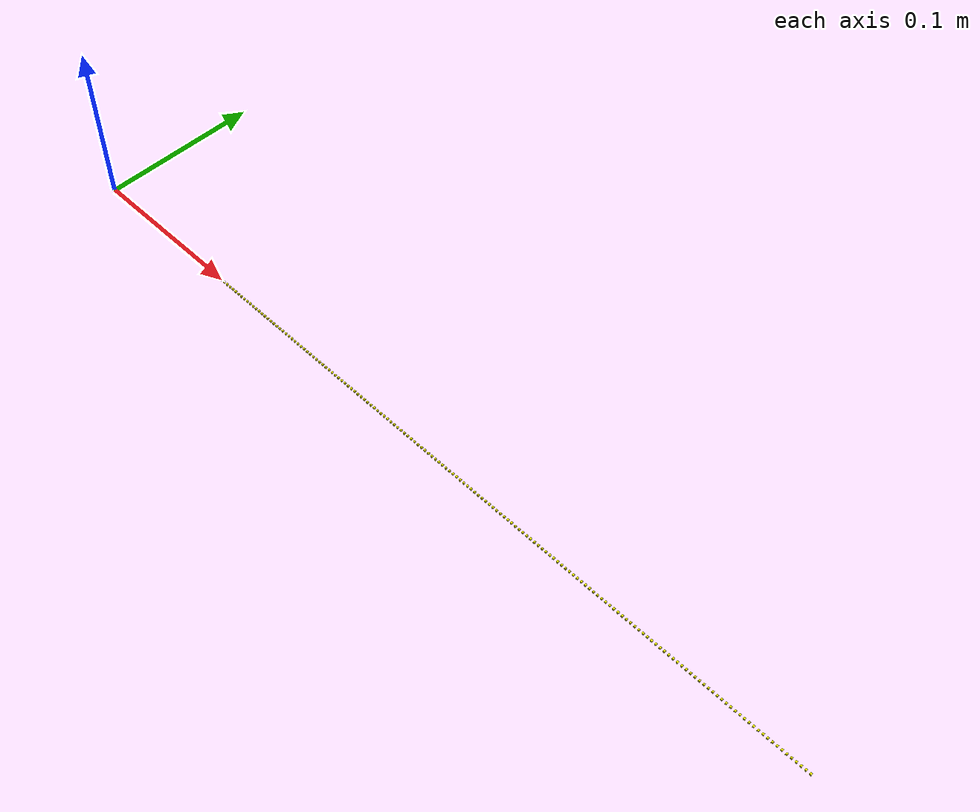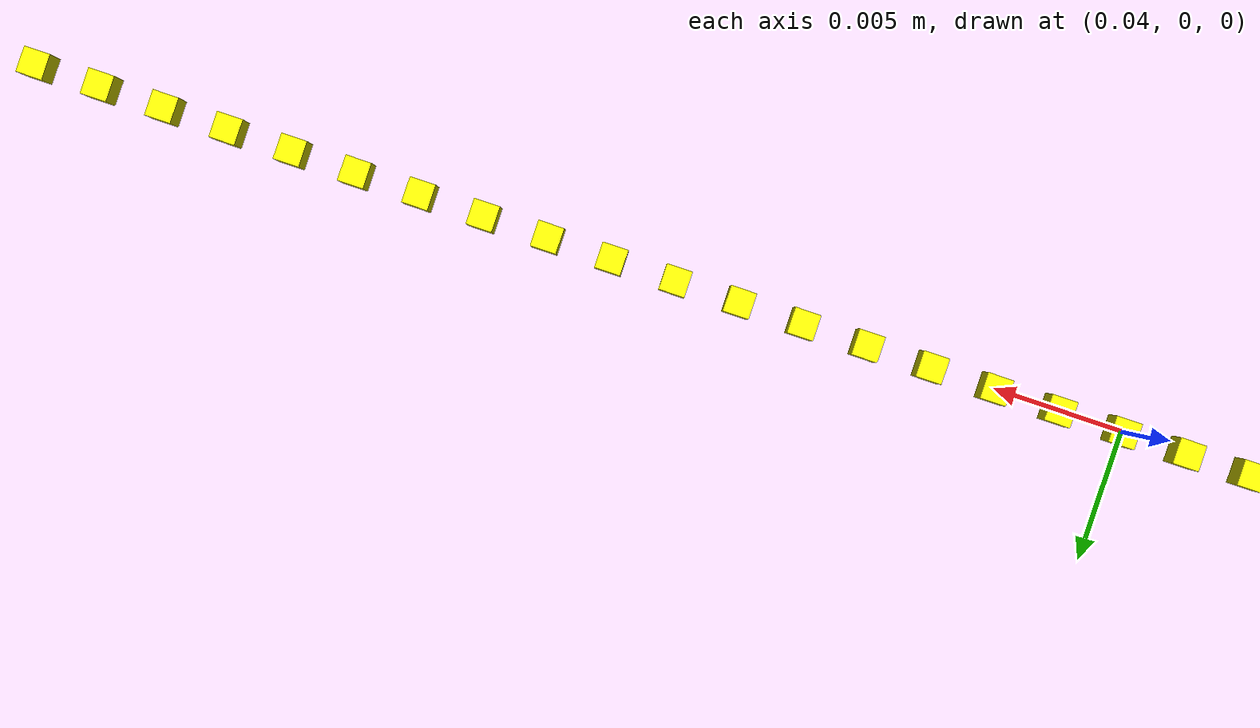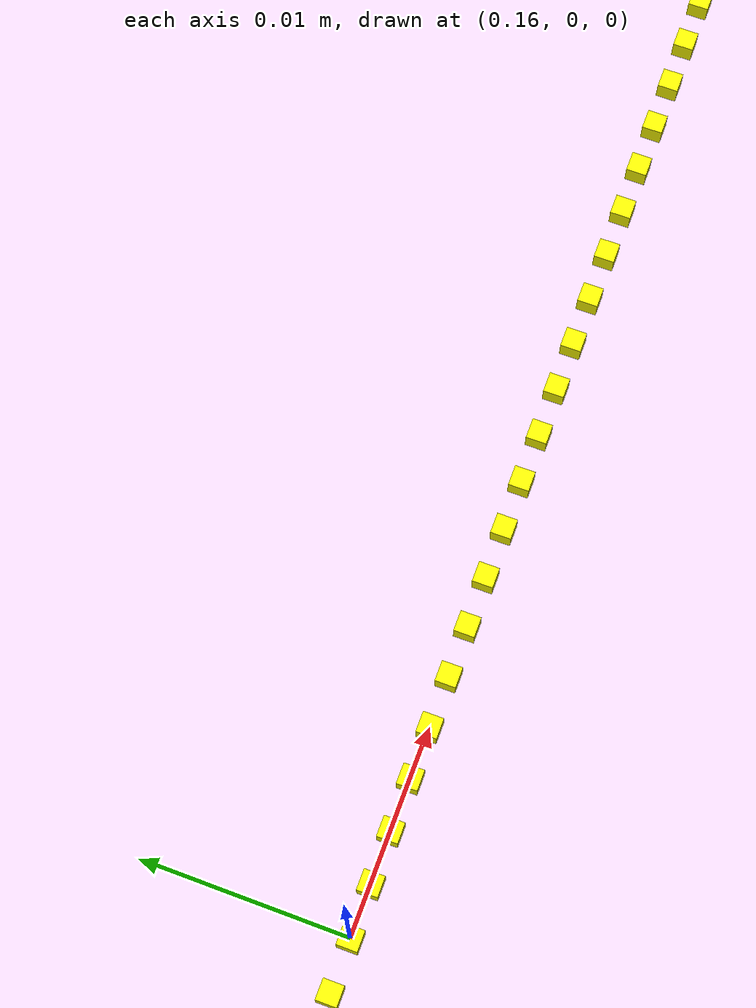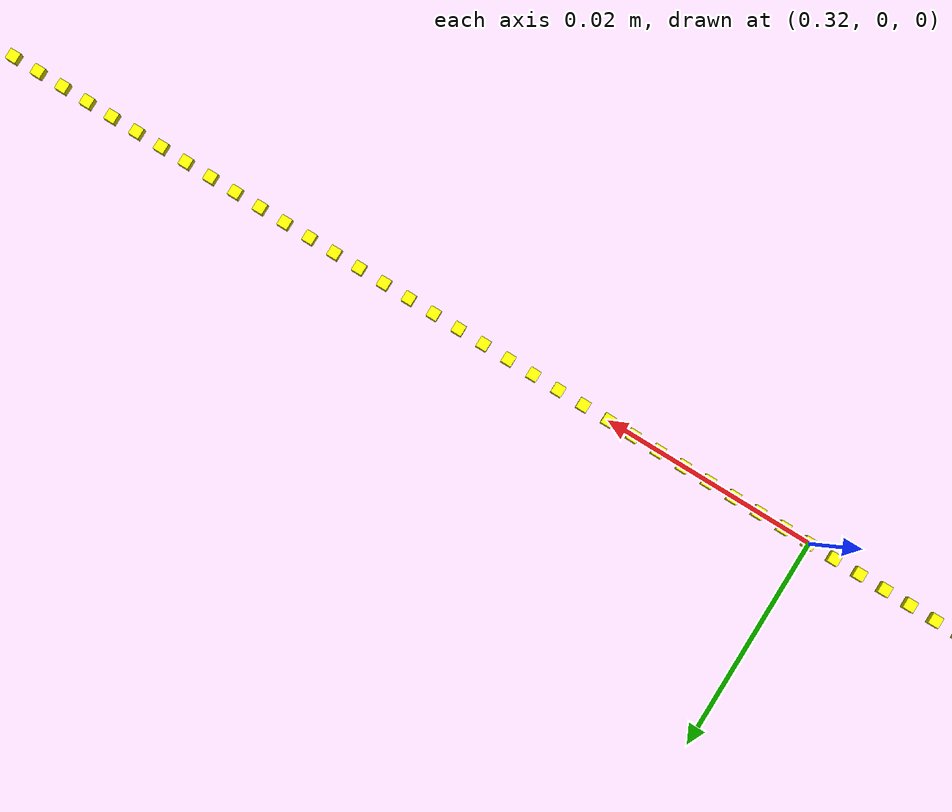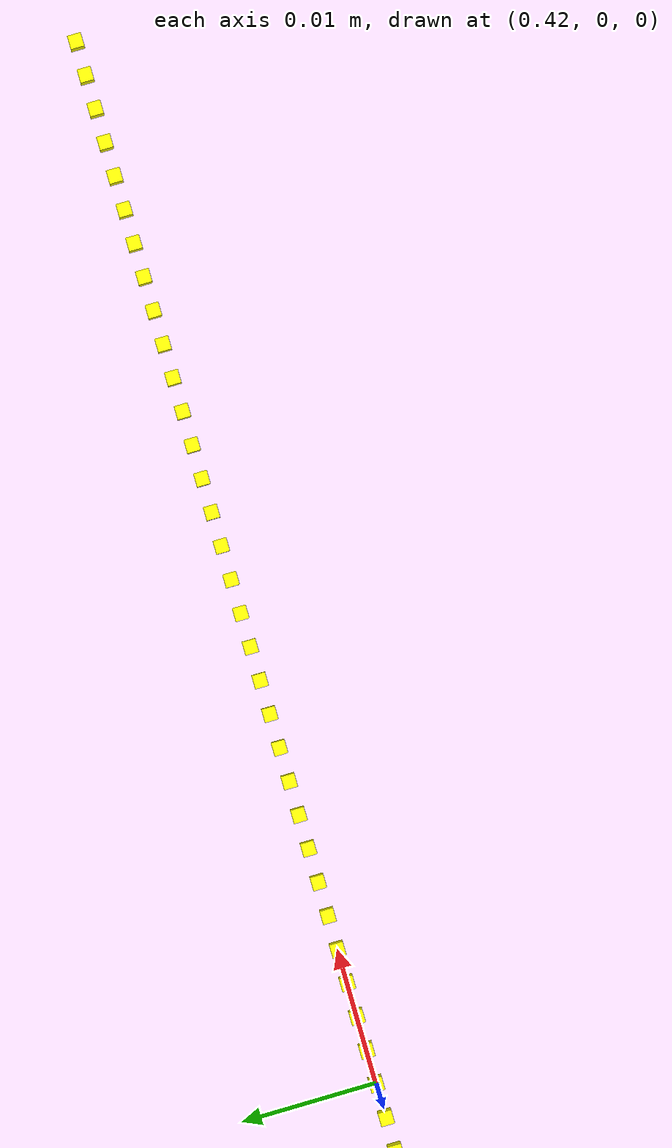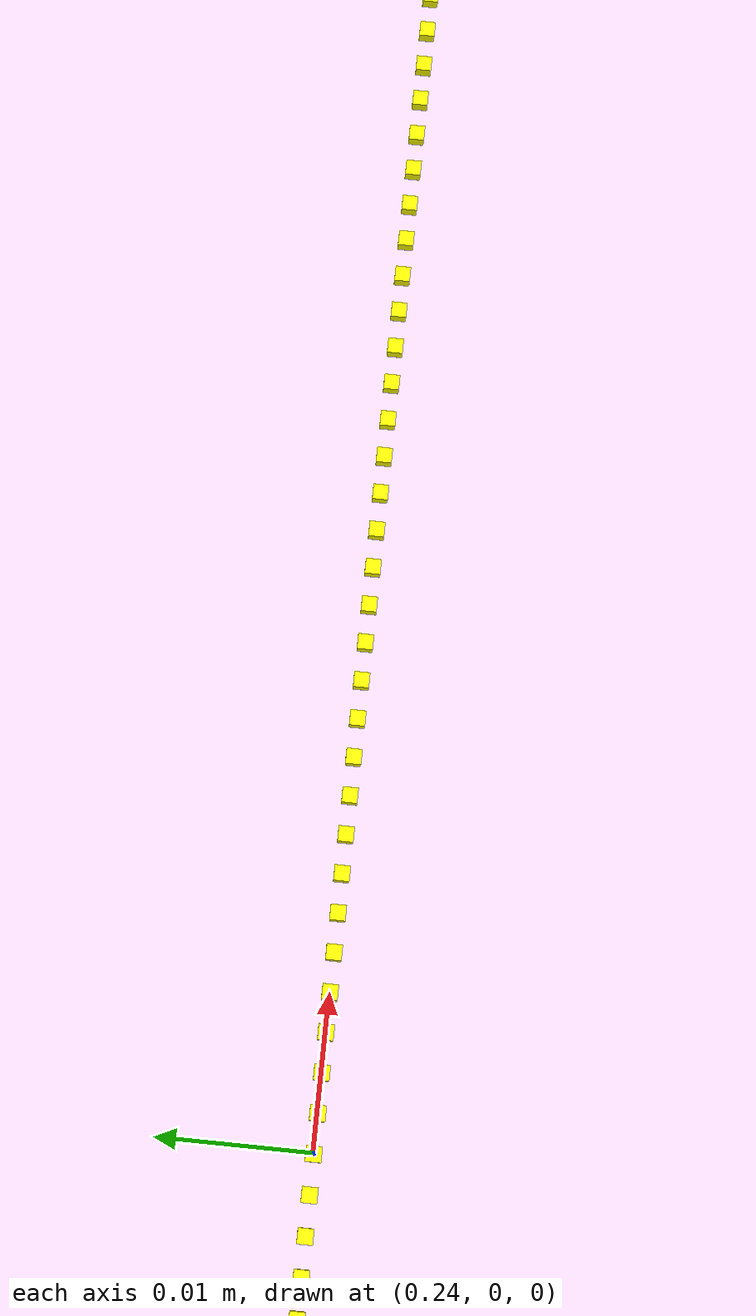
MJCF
<mujoco model="2D_UpperLimb">
  <compiler inertiafromgeom="auto" angle="radian" />
   <option timestep="0.0001" iterations="50" solver="PGS" integrator="Euler" gravity="0 0 0" collision="predefined">
     <flag energy="enable" />
   </option>
   <asset>
     <texture type="skybox" builtin="flat" rgb1="1 1 1" rgb2="1 1 1" width="100" height="100" />
      <material name="JointColor" rgba="1.0 1.0 0.0 1" />
      <material name="LimbColor" rgba="0.7 0.7 0.7 1" />
   </asset>
   <worldbody>
     <body name="cameramover" mocap="true" pos="0 0 0">
        <camera name="mycamera" pos="0.0 2.0 2.0" euler="1.5707 0 0" />
      </body>
      <body name="root" pos="0 0 0" euler="0 0 0">
        <joint ref="0" type="slide" name="sender" stiffness="1000" pos=" 0.0000 0 0" axis="1 0 0" />
         <geom type="box" name="mass1" mass="0.1" pos=" 0.0000 0 0" material="JointColor" size=" 0.0005 0.0005 0.0005" />
         <body name="node2" euler="0 0 0" pos=" 0.0025 0 0">
           <joint ref="0" type="slide" name="spring2" stiffness="1000" pos=" 0.0000 0 0" axis="1 0 0" />
            <geom type="box" name="mass2" mass="0.1" pos=" 0.0000 0 0" material="JointColor" size=" 0.0005 0.0005 0.0005" />
            <body name="node3" euler="0 0 0" pos=" 0.0025 0 0">
              <joint ref="0" type="slide" name="spring3" stiffness="1000" pos=" 0.0000 0 0" axis="1 0 0" />
               <geom type="box" name="mass3" mass="0.1" pos=" 0.0000 0 0" material="JointColor" size=" 0.0005 0.0005 0.0005" />
               <body name="node4" euler="0 0 0" pos=" 0.0025 0 0">
                 <joint ref="0" type="slide" name="spring4" stiffness="1000" pos=" 0.0000 0 0" axis="1 0 0" />
                  <geom type="box" name="mass4" mass="0.1" pos=" 0.0000 0 0" material="JointColor" size=" 0.0005 0.0005 0.0005" />
                  <body name="node5" euler="0 0 0" pos=" 0.0025 0 0">
                    <joint ref="0" type="slide" name="spring5" stiffness="1000" pos=" 0.0000 0 0" axis="1 0 0" />
                     <geom type="box" name="mass5" mass="0.1" pos=" 0.0000 0 0" material="JointColor" size=" 0.0005 0.0005 0.0005" />
                     <body name="node6" euler="0 0 0" pos=" 0.0025 0 0">
                       <joint ref="0" type="slide" name="spring6" stiffness="1000" pos=" 0.0000 0 0" axis="1 0 0" />
                        <geom type="box" name="mass6" mass="0.1" pos=" 0.0000 0 0" material="JointColor" size=" 0.0005 0.0005 0.0005" />
                        <body name="node7" euler="0 0 0" pos=" 0.0025 0 0">
                          <joint ref="0" type="slide" name="spring7" stiffness="1000" pos=" 0.0000 0 0" axis="1 0 0" />
                           <geom type="box" name="mass7" mass="0.1" pos=" 0.0000 0 0" material="JointColor" size=" 0.0005 0.0005 0.0005" />
                           <body name="node8" euler="0 0 0" pos=" 0.0025 0 0">
                             <joint ref="0" type="slide" name="spring8" stiffness="1000" pos=" 0.0000 0 0" axis="1 0 0" />
                              <geom type="box" name="mass8" mass="0.1" pos=" 0.0000 0 0" material="JointColor" size=" 0.0005 0.0005 0.0005" />
                              <body name="node9" euler="0 0 0" pos=" 0.0025 0 0">
                                <joint ref="0" type="slide" name="spring9" stiffness="1000" pos=" 0.0000 0 0" axis="1 0 0" />
                                 <geom type="box" name="mass9" mass="0.1" pos=" 0.0000 0 0" material="JointColor" size=" 0.0005 0.0005 0.0005" />
                                 <body name="node10" euler="0 0 0" pos=" 0.0025 0 0">
                                   <joint ref="0" type="slide" name="spring10" stiffness="1000" pos=" 0.0000 0 0" axis="1 0 0" />
                                    <geom type="box" name="mass10" mass="0.1" pos=" 0.0000 0 0" material="JointColor" size=" 0.0005 0.0005 0.0005" />
                                    <body name="node11" euler="0 0 0" pos=" 0.0025 0 0">
                                      <joint ref="0" type="slide" name="spring11" stiffness="1000" pos=" 0.0000 0 0" axis="1 0 0" />
                                       <geom type="box" name="mass11" mass="0.1" pos=" 0.0000 0 0" material="JointColor" size=" 0.0005 0.0005 0.0005" />
                                       <body name="node12" euler="0 0 0" pos=" 0.0025 0 0">
                                         <joint ref="0" type="slide" name="spring12" stiffness="1000" pos=" 0.0000 0 0" axis="1 0 0" />
                                          <geom type="box" name="mass12" mass="0.1" pos=" 0.0000 0 0" material="JointColor" size=" 0.0005 0.0005 0.0005" />
                                          <body name="node13" euler="0 0 0" pos=" 0.0025 0 0">
                                            <joint ref="0" type="slide" name="spring13" stiffness="1000" pos=" 0.0000 0 0" axis="1 0 0" />
                                             <geom type="box" name="mass13" mass="0.1" pos=" 0.0000 0 0" material="JointColor" size=" 0.0005 0.0005 0.0005" />
                                             <body name="node14" euler="0 0 0" pos=" 0.0025 0 0">
                                               <joint ref="0" type="slide" name="spring14" stiffness="1000" pos=" 0.0000 0 0" axis="1 0 0" />
                                                <geom type="box" name="mass14" mass="0.1" pos=" 0.0000 0 0" material="JointColor" size=" 0.0005 0.0005 0.0005" />
                                                <body name="node15" euler="0 0 0" pos=" 0.0025 0 0">
                                                  <joint ref="0" type="slide" name="spring15" stiffness="1000" pos=" 0.0000 0 0" axis="1 0 0" />
                                                   <geom type="box" name="mass15" mass="0.1" pos=" 0.0000 0 0" material="JointColor" size=" 0.0005 0.0005 0.0005" />
                                                   <body name="node16" euler="0 0 0" pos=" 0.0025 0 0">
                                                     <joint ref="0" type="slide" name="spring16" stiffness="1000" pos=" 0.0000 0 0" axis="1 0 0" />
                                                      <geom type="box" name="mass16" mass="0.1" pos=" 0.0000 0 0" material="JointColor" size=" 0.0005 0.0005 0.0005" />
                                                      <body name="node17" euler="0 0 0" pos=" 0.0025 0 0">
                                                        <joint ref="0" type="slide" name="spring17" stiffness="1000" pos=" 0.0000 0 0" axis="1 0 0" />
                                                         <geom type="box" name="mass17" mass="0.1" pos=" 0.0000 0 0" material="JointColor" size=" 0.0005 0.0005 0.0005" />
                                                         <body name="node18" euler="0 0 0" pos=" 0.0025 0 0">
                                                           <joint ref="0" type="slide" name="spring18" stiffness="1000" pos=" 0.0000 0 0" axis="1 0 0" />
                                                            <geom type="box" name="mass18" mass="0.1" pos=" 0.0000 0 0" material="JointColor" size=" 0.0005 0.0005 0.0005" />
                                                            <body name="node19" euler="0 0 0" pos=" 0.0025 0 0">
                                                              <joint ref="0" type="slide" name="spring19" stiffness="1000" pos=" 0.0000 0 0" axis="1 0 0" />
                                                               <geom type="box" name="mass19" mass="0.1" pos=" 0.0000 0 0" material="JointColor" size=" 0.0005 0.0005 0.0005" />
                                                               <body name="node20" euler="0 0 0" pos=" 0.0025 0 0">
                                                                 <joint ref="0" type="slide" name="spring20" stiffness="1000" pos=" 0.0000 0 0" axis="1 0 0" />
                                                                  <geom type="box" name="mass20" mass="0.1" pos=" 0.0000 0 0" material="JointColor" size=" 0.0005 0.0005 0.0005" />
                                                                  <body name="node21" euler="0 0 0" pos=" 0.0025 0 0">
                                                                    <joint ref="0" type="slide" name="spring21" stiffness="1000" pos=" 0.0000 0 0" axis="1 0 0" />
                                                                     <geom type="box" name="mass21" mass="0.1" pos=" 0.0000 0 0" material="JointColor" size=" 0.0005 0.0005 0.0005" />
                                                                     <body name="node22" euler="0 0 0" pos=" 0.0025 0 0">
                                                                       <joint ref="0" type="slide" name="spring22" stiffness="1000" pos=" 0.0000 0 0" axis="1 0 0" />
                                                                        <geom type="box" name="mass22" mass="0.1" pos=" 0.0000 0 0" material="JointColor" size=" 0.0005 0.0005 0.0005" />
                                                                        <body name="node23" euler="0 0 0" pos=" 0.0025 0 0">
                                                                          <joint ref="0" type="slide" name="spring23" stiffness="1000" pos=" 0.0000 0 0" axis="1 0 0" />
                                                                           <geom type="box" name="mass23" mass="0.1" pos=" 0.0000 0 0" material="JointColor" size=" 0.0005 0.0005 0.0005" />
                                                                           <body name="node24" euler="0 0 0" pos=" 0.0025 0 0">
                                                                             <joint ref="0" type="slide" name="spring24" stiffness="1000" pos=" 0.0000 0 0" axis="1 0 0" />
                                                                              <geom type="box" name="mass24" mass="0.1" pos=" 0.0000 0 0" material="JointColor" size=" 0.0005 0.0005 0.0005" />
                                                                              <body name="node25" euler="0 0 0" pos=" 0.0025 0 0">
                                                                                <joint ref="0" type="slide" name="spring25" stiffness="1000" pos=" 0.0000 0 0" axis="1 0 0" />
                                                                                 <geom type="box" name="mass25" mass="0.1" pos=" 0.0000 0 0" material="JointColor" size=" 0.0005 0.0005 0.0005" />
                                                                                 <body name="node26" euler="0 0 0" pos=" 0.0025 0 0">
                                                                                   <joint ref="0" type="slide" name="spring26" stiffness="1000" pos=" 0.0000 0 0" axis="1 0 0" />
                                                                                    <geom type="box" name="mass26" mass="0.1" pos=" 0.0000 0 0" material="JointColor" size=" 0.0005 0.0005 0.0005" />
                                                                                    <body name="node27" euler="0 0 0" pos=" 0.0025 0 0">
                                                                                      <joint ref="0" type="slide" name="spring27" stiffness="1000" pos=" 0.0000 0 0" axis="1 0 0" />
                                                                                       <geom type="box" name="mass27" mass="0.1" pos=" 0.0000 0 0" material="JointColor" size=" 0.0005 0.0005 0.0005" />
                                                                                       <body name="node28" euler="0 0 0" pos=" 0.0025 0 0">
                                                                                         <joint ref="0" type="slide" name="spring28" stiffness="1000" pos=" 0.0000 0 0" axis="1 0 0" />
                                                                                          <geom type="box" name="mass28" mass="0.1" pos=" 0.0000 0 0" material="JointColor" size=" 0.0005 0.0005 0.0005" />
                                                                                          <body name="node29" euler="0 0 0" pos=" 0.0025 0 0">
                                                                                            <joint ref="0" type="slide" name="spring29" stiffness="1000" pos=" 0.0000 0 0" axis="1 0 0" />
                                                                                             <geom type="box" name="mass29" mass="0.1" pos=" 0.0000 0 0" material="JointColor" size=" 0.0005 0.0005 0.0005" />
                                                                                             <body name="node30" euler="0 0 0" pos=" 0.0025 0 0">
                                                                                               <joint ref="0" type="slide" name="spring30" stiffness="1000" pos=" 0.0000 0 0" axis="1 0 0" />
                                                                                                <geom type="box" name="mass30" mass="0.1" pos=" 0.0000 0 0" material="JointColor" size=" 0.0005 0.0005 0.0005" />
                                                                                                <body name="node31" euler="0 0 0" pos=" 0.0025 0 0">
                                                                                                  <joint ref="0" type="slide" name="spring31" stiffness="1000" pos=" 0.0000 0 0" axis="1 0 0" />
                                                                                                   <geom type="box" name="mass31" mass="0.1" pos=" 0.0000 0 0" material="JointColor" size=" 0.0005 0.0005 0.0005" />
                                                                                                   <body name="node32" euler="0 0 0" pos=" 0.0025 0 0">
                                                                                                     <joint ref="0" type="slide" name="spring32" stiffness="1000" pos=" 0.0000 0 0" axis="1 0 0" />
                                                                                                      <geom type="box" name="mass32" mass="0.1" pos=" 0.0000 0 0" material="JointColor" size=" 0.0005 0.0005 0.0005" />
                                                                                                      <body name="node33" euler="0 0 0" pos=" 0.0025 0 0">
                                                                                                        <joint ref="0" type="slide" name="spring33" stiffness="1000" pos=" 0.0000 0 0" axis="1 0 0" />
                                                                                                         <geom type="box" name="mass33" mass="0.1" pos=" 0.0000 0 0" material="JointColor" size=" 0.0005 0.0005 0.0005" />
                                                                                                         <body name="node34" euler="0 0 0" pos=" 0.0025 0 0">
                                                                                                           <joint ref="0" type="slide" name="spring34" stiffness="1000" pos=" 0.0000 0 0" axis="1 0 0" />
                                                                                                            <geom type="box" name="mass34" mass="0.1" pos=" 0.0000 0 0" material="JointColor" size=" 0.0005 0.0005 0.0005" />
                                                                                                            <body name="node35" euler="0 0 0" pos=" 0.0025 0 0">
                                                                                                              <joint ref="0" type="slide" name="spring35" stiffness="1000" pos=" 0.0000 0 0" axis="1 0 0" />
                                                                                                               <geom type="box" name="mass35" mass="0.1" pos=" 0.0000 0 0" material="JointColor" size=" 0.0005 0.0005 0.0005" />
                                                                                                               <body name="node36" euler="0 0 0" pos=" 0.0025 0 0">
                                                                                                                 <joint ref="0" type="slide" name="spring36" stiffness="1000" pos=" 0.0000 0 0" axis="1 0 0" />
                                                                                                                  <geom type="box" name="mass36" mass="0.1" pos=" 0.0000 0 0" material="JointColor" size=" 0.0005 0.0005 0.0005" />
                                                                                                                  <body name="node37" euler="0 0 0" pos=" 0.0025 0 0">
                                                                                                                    <joint ref="0" type="slide" name="spring37" stiffness="1000" pos=" 0.0000 0 0" axis="1 0 0" />
                                                                                                                     <geom type="box" name="mass37" mass="0.1" pos=" 0.0000 0 0" material="JointColor" size=" 0.0005 0.0005 0.0005" />
                                                                                                                     <body name="node38" euler="0 0 0" pos=" 0.0025 0 0">
                                                                                                                       <joint ref="0" type="slide" name="spring38" stiffness="1000" pos=" 0.0000 0 0" axis="1 0 0" />
                                                                                                                        <geom type="box" name="mass38" mass="0.1" pos=" 0.0000 0 0" material="JointColor" size=" 0.0005 0.0005 0.0005" />
                                                                                                                        <body name="node39" euler="0 0 0" pos=" 0.0025 0 0">
                                                                                                                          <joint ref="0" type="slide" name="spring39" stiffness="1000" pos=" 0.0000 0 0" axis="1 0 0" />
                                                                                                                           <geom type="box" name="mass39" mass="0.1" pos=" 0.0000 0 0" material="JointColor" size=" 0.0005 0.0005 0.0005" />
                                                                                                                           <body name="node40" euler="0 0 0" pos=" 0.0025 0 0">
                                                                                                                             <joint ref="0" type="slide" name="spring40" stiffness="1000" pos=" 0.0000 0 0" axis="1 0 0" />
                                                                                                                              <geom type="box" name="mass40" mass="0.1" pos=" 0.0000 0 0" material="JointColor" size=" 0.0005 0.0005 0.0005" />
                                                                                                                              <body name="node41" euler="0 0 0" pos=" 0.0025 0 0">
                                                                                                                                <joint ref="0" type="slide" name="spring41" stiffness="1000" pos=" 0.0000 0 0" axis="1 0 0" />
                                                                                                                                 <geom type="box" name="mass41" mass="0.1" pos=" 0.0000 0 0" material="JointColor" size=" 0.0005 0.0005 0.0005" />
                                                                                                                                 <body name="node42" euler="0 0 0" pos=" 0.0025 0 0">
                                                                                                                                   <joint ref="0" type="slide" name="spring42" stiffness="1000" pos=" 0.0000 0 0" axis="1 0 0" />
                                                                                                                                    <geom type="box" name="mass42" mass="0.1" pos=" 0.0000 0 0" material="JointColor" size=" 0.0005 0.0005 0.0005" />
                                                                                                                                    <body name="node43" euler="0 0 0" pos=" 0.0025 0 0">
                                                                                                                                      <joint ref="0" type="slide" name="spring43" stiffness="1000" pos=" 0.0000 0 0" axis="1 0 0" />
                                                                                                                                       <geom type="box" name="mass43" mass="0.1" pos=" 0.0000 0 0" material="JointColor" size=" 0.0005 0.0005 0.0005" />
                                                                                                                                       <body name="node44" euler="0 0 0" pos=" 0.0025 0 0">
                                                                                                                                         <joint ref="0" type="slide" name="spring44" stiffness="1000" pos=" 0.0000 0 0" axis="1 0 0" />
                                                                                                                                          <geom type="box" name="mass44" mass="0.1" pos=" 0.0000 0 0" material="JointColor" size=" 0.0005 0.0005 0.0005" />
                                                                                                                                          <body name="node45" euler="0 0 0" pos=" 0.0025 0 0">
                                                                                                                                            <joint ref="0" type="slide" name="spring45" stiffness="1000" pos=" 0.0000 0 0" axis="1 0 0" />
                                                                                                                                             <geom type="box" name="mass45" mass="0.1" pos=" 0.0000 0 0" material="JointColor" size=" 0.0005 0.0005 0.0005" />
                                                                                                                                             <body name="node46" euler="0 0 0" pos=" 0.0025 0 0">
                                                                                                                                               <joint ref="0" type="slide" name="spring46" stiffness="1000" pos=" 0.0000 0 0" axis="1 0 0" />
                                                                                                                                                <geom type="box" name="mass46" mass="0.1" pos=" 0.0000 0 0" material="JointColor" size=" 0.0005 0.0005 0.0005" />
                                                                                                                                                <body name="node47" euler="0 0 0" pos=" 0.0025 0 0">
                                                                                                                                                  <joint ref="0" type="slide" name="spring47" stiffness="1000" pos=" 0.0000 0 0" axis="1 0 0" />
                                                                                                                                                   <geom type="box" name="mass47" mass="0.1" pos=" 0.0000 0 0" material="JointColor" size=" 0.0005 0.0005 0.0005" />
                                                                                                                                                   <body name="node48" euler="0 0 0" pos=" 0.0025 0 0">
                                                                                                                                                     <joint ref="0" type="slide" name="spring48" stiffness="1000" pos=" 0.0000 0 0" axis="1 0 0" />
                                                                                                                                                      <geom type="box" name="mass48" mass="0.1" pos=" 0.0000 0 0" material="JointColor" size=" 0.0005 0.0005 0.0005" />
                                                                                                                                                      <body name="node49" euler="0 0 0" pos=" 0.0025 0 0">
                                                                                                                                                        <joint ref="0" type="slide" name="spring49" stiffness="1000" pos=" 0.0000 0 0" axis="1 0 0" />
                                                                                                                                                         <geom type="box" name="mass49" mass="0.1" pos=" 0.0000 0 0" material="JointColor" size=" 0.0005 0.0005 0.0005" />
                                                                                                                                                         <body name="node50" euler="0 0 0" pos=" 0.0025 0 0">
                                                                                                                                                           <joint ref="0" type="slide" name="spring50" stiffness="1000" pos=" 0.0000 0 0" axis="1 0 0" />
                                                                                                                                                            <geom type="box" name="mass50" mass="0.1" pos=" 0.0000 0 0" material="JointColor" size=" 0.0005 0.0005 0.0005" />
                                                                                                                                                            <body name="node51" euler="0 0 0" pos=" 0.0025 0 0">
                                                                                                                                                              <joint ref="0" type="slide" name="spring51" stiffness="1000" pos=" 0.0000 0 0" axis="1 0 0" />
                                                                                                                                                               <geom type="box" name="mass51" mass="0.1" pos=" 0.0000 0 0" material="JointColor" size=" 0.0005 0.0005 0.0005" />
                                                                                                                                                               <body name="node52" euler="0 0 0" pos=" 0.0025 0 0">
                                                                                                                                                                 <joint ref="0" type="slide" name="spring52" stiffness="1000" pos=" 0.0000 0 0" axis="1 0 0" />
                                                                                                                                                                  <geom type="box" name="mass52" mass="0.1" pos=" 0.0000 0 0" material="JointColor" size=" 0.0005 0.0005 0.0005" />
                                                                                                                                                                  <body name="node53" euler="0 0 0" pos=" 0.0025 0 0">
                                                                                                                                                                    <joint ref="0" type="slide" name="spring53" stiffness="1000" pos=" 0.0000 0 0" axis="1 0 0" />
                                                                                                                                                                     <geom type="box" name="mass53" mass="0.1" pos=" 0.0000 0 0" material="JointColor" size=" 0.0005 0.0005 0.0005" />
                                                                                                                                                                     <body name="node54" euler="0 0 0" pos=" 0.0025 0 0">
                                                                                                                                                                       <joint ref="0" type="slide" name="spring54" stiffness="1000" pos=" 0.0000 0 0" axis="1 0 0" />
                                                                                                                                                                        <geom type="box" name="mass54" mass="0.1" pos=" 0.0000 0 0" material="JointColor" size=" 0.0005 0.0005 0.0005" />
                                                                                                                                                                        <body name="node55" euler="0 0 0" pos=" 0.0025 0 0">
                                                                                                                                                                          <joint ref="0" type="slide" name="spring55" stiffness="1000" pos=" 0.0000 0 0" axis="1 0 0" />
                                                                                                                                                                           <geom type="box" name="mass55" mass="0.1" pos=" 0.0000 0 0" material="JointColor" size=" 0.0005 0.0005 0.0005" />
                                                                                                                                                                           <body name="node56" euler="0 0 0" pos=" 0.0025 0 0">
                                                                                                                                                                             <joint ref="0" type="slide" name="spring56" stiffness="1000" pos=" 0.0000 0 0" axis="1 0 0" />
                                                                                                                                                                              <geom type="box" name="mass56" mass="0.1" pos=" 0.0000 0 0" material="JointColor" size=" 0.0005 0.0005 0.0005" />
                                                                                                                                                                              <body name="node57" euler="0 0 0" pos=" 0.0025 0 0">
                                                                                                                                                                                <joint ref="0" type="slide" name="spring57" stiffness="1000" pos=" 0.0000 0 0" axis="1 0 0" />
                                                                                                                                                                                 <geom type="box" name="mass57" mass="0.1" pos=" 0.0000 0 0" material="JointColor" size=" 0.0005 0.0005 0.0005" />
                                                                                                                                                                                 <body name="node58" euler="0 0 0" pos=" 0.0025 0 0">
                                                                                                                                                                                   <joint ref="0" type="slide" name="spring58" stiffness="1000" pos=" 0.0000 0 0" axis="1 0 0" />
                                                                                                                                                                                    <geom type="box" name="mass58" mass="0.1" pos=" 0.0000 0 0" material="JointColor" size=" 0.0005 0.0005 0.0005" />
                                                                                                                                                                                    <body name="node59" euler="0 0 0" pos=" 0.0025 0 0">
                                                                                                                                                                                      <joint ref="0" type="slide" name="spring59" stiffness="1000" pos=" 0.0000 0 0" axis="1 0 0" />
                                                                                                                                                                                       <geom type="box" name="mass59" mass="0.1" pos=" 0.0000 0 0" material="JointColor" size=" 0.0005 0.0005 0.0005" />
                                                                                                                                                                                       <body name="node60" euler="0 0 0" pos=" 0.0025 0 0">
                                                                                                                                                                                         <joint ref="0" type="slide" name="spring60" stiffness="1000" pos=" 0.0000 0 0" axis="1 0 0" />
                                                                                                                                                                                          <geom type="box" name="mass60" mass="0.1" pos=" 0.0000 0 0" material="JointColor" size=" 0.0005 0.0005 0.0005" />
                                                                                                                                                                                          <body name="node61" euler="0 0 0" pos=" 0.0025 0 0">
                                                                                                                                                                                            <joint ref="0" type="slide" name="spring61" stiffness="1000" pos=" 0.0000 0 0" axis="1 0 0" />
                                                                                                                                                                                             <geom type="box" name="mass61" mass="0.1" pos=" 0.0000 0 0" material="JointColor" size=" 0.0005 0.0005 0.0005" />
                                                                                                                                                                                             <body name="node62" euler="0 0 0" pos=" 0.0025 0 0">
                                                                                                                                                                                               <joint ref="0" type="slide" name="spring62" stiffness="1000" pos=" 0.0000 0 0" axis="1 0 0" />
                                                                                                                                                                                                <geom type="box" name="mass62" mass="0.1" pos=" 0.0000 0 0" material="JointColor" size=" 0.0005 0.0005 0.0005" />
                                                                                                                                                                                                <body name="node63" euler="0 0 0" pos=" 0.0025 0 0">
                                                                                                                                                                                                  <joint ref="0" type="slide" name="spring63" stiffness="1000" pos=" 0.0000 0 0" axis="1 0 0" />
                                                                                                                                                                                                   <geom type="box" name="mass63" mass="0.1" pos=" 0.0000 0 0" material="JointColor" size=" 0.0005 0.0005 0.0005" />
                                                                                                                                                                                                   <body name="node64" euler="0 0 0" pos=" 0.0025 0 0">
                                                                                                                                                                                                     <joint ref="0" type="slide" name="spring64" stiffness="1000" pos=" 0.0000 0 0" axis="1 0 0" />
                                                                                                                                                                                                      <geom type="box" name="mass64" mass="0.1" pos=" 0.0000 0 0" material="JointColor" size=" 0.0005 0.0005 0.0005" />
                                                                                                                                                                                                      <body name="node65" euler="0 0 0" pos=" 0.0025 0 0">
                                                                                                                                                                                                        <joint ref="0" type="slide" name="spring65" stiffness="1000" pos=" 0.0000 0 0" axis="1 0 0" />
                                                                                                                                                                                                         <geom type="box" name="mass65" mass="0.1" pos=" 0.0000 0 0" material="JointColor" size=" 0.0005 0.0005 0.0005" />
                                                                                                                                                                                                         <body name="node66" euler="0 0 0" pos=" 0.0025 0 0">
                                                                                                                                                                                                           <joint ref="0" type="slide" name="spring66" stiffness="1000" pos=" 0.0000 0 0" axis="1 0 0" />
                                                                                                                                                                                                            <geom type="box" name="mass66" mass="0.1" pos=" 0.0000 0 0" material="JointColor" size=" 0.0005 0.0005 0.0005" />
                                                                                                                                                                                                            <body name="node67" euler="0 0 0" pos=" 0.0025 0 0">
                                                                                                                                                                                                              <joint ref="0" type="slide" name="spring67" stiffness="1000" pos=" 0.0000 0 0" axis="1 0 0" />
                                                                                                                                                                                                               <geom type="box" name="mass67" mass="0.1" pos=" 0.0000 0 0" material="JointColor" size=" 0.0005 0.0005 0.0005" />
                                                                                                                                                                                                               <body name="node68" euler="0 0 0" pos=" 0.0025 0 0">
                                                                                                                                                                                                                 <joint ref="0" type="slide" name="spring68" stiffness="1000" pos=" 0.0000 0 0" axis="1 0 0" />
                                                                                                                                                                                                                  <geom type="box" name="mass68" mass="0.1" pos=" 0.0000 0 0" material="JointColor" size=" 0.0005 0.0005 0.0005" />
                                                                                                                                                                                                                  <body name="node69" euler="0 0 0" pos=" 0.0025 0 0">
                                                                                                                                                                                                                    <joint ref="0" type="slide" name="spring69" stiffness="1000" pos=" 0.0000 0 0" axis="1 0 0" />
                                                                                                                                                                                                                     <geom type="box" name="mass69" mass="0.1" pos=" 0.0000 0 0" material="JointColor" size=" 0.0005 0.0005 0.0005" />
                                                                                                                                                                                                                     <body name="node70" euler="0 0 0" pos=" 0.0025 0 0">
                                                                                                                                                                                                                       <joint ref="0" type="slide" name="spring70" stiffness="1000" pos=" 0.0000 0 0" axis="1 0 0" />
                                                                                                                                                                                                                        <geom type="box" name="mass70" mass="0.1" pos=" 0.0000 0 0" material="JointColor" size=" 0.0005 0.0005 0.0005" />
                                                                                                                                                                                                                        <body name="node71" euler="0 0 0" pos=" 0.0025 0 0">
                                                                                                                                                                                                                          <joint ref="0" type="slide" name="spring71" stiffness="1000" pos=" 0.0000 0 0" axis="1 0 0" />
                                                                                                                                                                                                                           <geom type="box" name="mass71" mass="0.1" pos=" 0.0000 0 0" material="JointColor" size=" 0.0005 0.0005 0.0005" />
                                                                                                                                                                                                                           <body name="node72" euler="0 0 0" pos=" 0.0025 0 0">
                                                                                                                                                                                                                             <joint ref="0" type="slide" name="spring72" stiffness="1000" pos=" 0.0000 0 0" axis="1 0 0" />
                                                                                                                                                                                                                              <geom type="box" name="mass72" mass="0.1" pos=" 0.0000 0 0" material="JointColor" size=" 0.0005 0.0005 0.0005" />
                                                                                                                                                                                                                              <body name="node73" euler="0 0 0" pos=" 0.0025 0 0">
                                                                                                                                                                                                                                <joint ref="0" type="slide" name="spring73" stiffness="1000" pos=" 0.0000 0 0" axis="1 0 0" />
                                                                                                                                                                                                                                 <geom type="box" name="mass73" mass="0.1" pos=" 0.0000 0 0" material="JointColor" size=" 0.0005 0.0005 0.0005" />
                                                                                                                                                                                                                                 <body name="node74" euler="0 0 0" pos=" 0.0025 0 0">
                                                                                                                                                                                                                                   <joint ref="0" type="slide" name="spring74" stiffness="1000" pos=" 0.0000 0 0" axis="1 0 0" />
                                                                                                                                                                                                                                    <geom type="box" name="mass74" mass="0.1" pos=" 0.0000 0 0" material="JointColor" size=" 0.0005 0.0005 0.0005" />
                                                                                                                                                                                                                                    <body name="node75" euler="0 0 0" pos=" 0.0025 0 0">
                                                                                                                                                                                                                                      <joint ref="0" type="slide" name="spring75" stiffness="1000" pos=" 0.0000 0 0" axis="1 0 0" />
                                                                                                                                                                                                                                       <geom type="box" name="mass75" mass="0.1" pos=" 0.0000 0 0" material="JointColor" size=" 0.0005 0.0005 0.0005" />
                                                                                                                                                                                                                                       <body name="node76" euler="0 0 0" pos=" 0.0025 0 0">
                                                                                                                                                                                                                                         <joint ref="0" type="slide" name="spring76" stiffness="1000" pos=" 0.0000 0 0" axis="1 0 0" />
                                                                                                                                                                                                                                          <geom type="box" name="mass76" mass="0.1" pos=" 0.0000 0 0" material="JointColor" size=" 0.0005 0.0005 0.0005" />
                                                                                                                                                                                                                                          <body name="node77" euler="0 0 0" pos=" 0.0025 0 0">
                                                                                                                                                                                                                                            <joint ref="0" type="slide" name="spring77" stiffness="1000" pos=" 0.0000 0 0" axis="1 0 0" />
                                                                                                                                                                                                                                             <geom type="box" name="mass77" mass="0.1" pos=" 0.0000 0 0" material="JointColor" size=" 0.0005 0.0005 0.0005" />
                                                                                                                                                                                                                                             <body name="node78" euler="0 0 0" pos=" 0.0025 0 0">
                                                                                                                                                                                                                                               <joint ref="0" type="slide" name="spring78" stiffness="1000" pos=" 0.0000 0 0" axis="1 0 0" />
                                                                                                                                                                                                                                                <geom type="box" name="mass78" mass="0.1" pos=" 0.0000 0 0" material="JointColor" size=" 0.0005 0.0005 0.0005" />
                                                                                                                                                                                                                                                <body name="node79" euler="0 0 0" pos=" 0.0025 0 0">
                                                                                                                                                                                                                                                  <joint ref="0" type="slide" name="spring79" stiffness="1000" pos=" 0.0000 0 0" axis="1 0 0" />
                                                                                                                                                                                                                                                   <geom type="box" name="mass79" mass="0.1" pos=" 0.0000 0 0" material="JointColor" size=" 0.0005 0.0005 0.0005" />
                                                                                                                                                                                                                                                   <body name="node80" euler="0 0 0" pos=" 0.0025 0 0">
                                                                                                                                                                                                                                                     <joint ref="0" type="slide" name="spring80" stiffness="1000" pos=" 0.0000 0 0" axis="1 0 0" />
                                                                                                                                                                                                                                                      <geom type="box" name="mass80" mass="0.1" pos=" 0.0000 0 0" material="JointColor" size=" 0.0005 0.0005 0.0005" />
                                                                                                                                                                                                                                                      <body name="node81" euler="0 0 0" pos=" 0.0025 0 0">
                                                                                                                                                                                                                                                        <joint ref="0" type="slide" name="spring81" stiffness="1000" pos=" 0.0000 0 0" axis="1 0 0" />
                                                                                                                                                                                                                                                         <geom type="box" name="mass81" mass="0.1" pos=" 0.0000 0 0" material="JointColor" size=" 0.0005 0.0005 0.0005" />
                                                                                                                                                                                                                                                         <body name="node82" euler="0 0 0" pos=" 0.0025 0 0">
                                                                                                                                                                                                                                                           <joint ref="0" type="slide" name="spring82" stiffness="1000" pos=" 0.0000 0 0" axis="1 0 0" />
                                                                                                                                                                                                                                                            <geom type="box" name="mass82" mass="0.1" pos=" 0.0000 0 0" material="JointColor" size=" 0.0005 0.0005 0.0005" />
                                                                                                                                                                                                                                                            <body name="node83" euler="0 0 0" pos=" 0.0025 0 0">
                                                                                                                                                                                                                                                              <joint ref="0" type="slide" name="spring83" stiffness="1000" pos=" 0.0000 0 0" axis="1 0 0" />
                                                                                                                                                                                                                                                               <geom type="box" name="mass83" mass="0.1" pos=" 0.0000 0 0" material="JointColor" size=" 0.0005 0.0005 0.0005" />
                                                                                                                                                                                                                                                               <body name="node84" euler="0 0 0" pos=" 0.0025 0 0">
                                                                                                                                                                                                                                                                 <joint ref="0" type="slide" name="spring84" stiffness="1000" pos=" 0.0000 0 0" axis="1 0 0" />
                                                                                                                                                                                                                                                                  <geom type="box" name="mass84" mass="0.1" pos=" 0.0000 0 0" material="JointColor" size=" 0.0005 0.0005 0.0005" />
                                                                                                                                                                                                                                                                  <body name="node85" euler="0 0 0" pos=" 0.0025 0 0">
                                                                                                                                                                                                                                                                    <joint ref="0" type="slide" name="spring85" stiffness="1000" pos=" 0.0000 0 0" axis="1 0 0" />
                                                                                                                                                                                                                                                                     <geom type="box" name="mass85" mass="0.1" pos=" 0.0000 0 0" material="JointColor" size=" 0.0005 0.0005 0.0005" />
                                                                                                                                                                                                                                                                     <body name="node86" euler="0 0 0" pos=" 0.0025 0 0">
                                                                                                                                                                                                                                                                       <joint ref="0" type="slide" name="spring86" stiffness="1000" pos=" 0.0000 0 0" axis="1 0 0" />
                                                                                                                                                                                                                                                                        <geom type="box" name="mass86" mass="0.1" pos=" 0.0000 0 0" material="JointColor" size=" 0.0005 0.0005 0.0005" />
                                                                                                                                                                                                                                                                        <body name="node87" euler="0 0 0" pos=" 0.0025 0 0">
                                                                                                                                                                                                                                                                          <joint ref="0" type="slide" name="spring87" stiffness="1000" pos=" 0.0000 0 0" axis="1 0 0" />
                                                                                                                                                                                                                                                                           <geom type="box" name="mass87" mass="0.1" pos=" 0.0000 0 0" material="JointColor" size=" 0.0005 0.0005 0.0005" />
                                                                                                                                                                                                                                                                           <body name="node88" euler="0 0 0" pos=" 0.0025 0 0">
                                                                                                                                                                                                                                                                             <joint ref="0" type="slide" name="spring88" stiffness="1000" pos=" 0.0000 0 0" axis="1 0 0" />
                                                                                                                                                                                                                                                                              <geom type="box" name="mass88" mass="0.1" pos=" 0.0000 0 0" material="JointColor" size=" 0.0005 0.0005 0.0005" />
                                                                                                                                                                                                                                                                              <body name="node89" euler="0 0 0" pos=" 0.0025 0 0">
                                                                                                                                                                                                                                                                                <joint ref="0" type="slide" name="spring89" stiffness="1000" pos=" 0.0000 0 0" axis="1 0 0" />
                                                                                                                                                                                                                                                                                 <geom type="box" name="mass89" mass="0.1" pos=" 0.0000 0 0" material="JointColor" size=" 0.0005 0.0005 0.0005" />
                                                                                                                                                                                                                                                                                 <body name="node90" euler="0 0 0" pos=" 0.0025 0 0">
                                                                                                                                                                                                                                                                                   <joint ref="0" type="slide" name="spring90" stiffness="1000" pos=" 0.0000 0 0" axis="1 0 0" />
                                                                                                                                                                                                                                                                                    <geom type="box" name="mass90" mass="0.1" pos=" 0.0000 0 0" material="JointColor" size=" 0.0005 0.0005 0.0005" />
                                                                                                                                                                                                                                                                                    <body name="node91" euler="0 0 0" pos=" 0.0025 0 0">
                                                                                                                                                                                                                                                                                      <joint ref="0" type="slide" name="spring91" stiffness="1000" pos=" 0.0000 0 0" axis="1 0 0" />
                                                                                                                                                                                                                                                                                       <geom type="box" name="mass91" mass="0.1" pos=" 0.0000 0 0" material="JointColor" size=" 0.0005 0.0005 0.0005" />
                                                                                                                                                                                                                                                                                       <body name="node92" euler="0 0 0" pos=" 0.0025 0 0">
                                                                                                                                                                                                                                                                                         <joint ref="0" type="slide" name="spring92" stiffness="1000" pos=" 0.0000 0 0" axis="1 0 0" />
                                                                                                                                                                                                                                                                                          <geom type="box" name="mass92" mass="0.1" pos=" 0.0000 0 0" material="JointColor" size=" 0.0005 0.0005 0.0005" />
                                                                                                                                                                                                                                                                                          <body name="node93" euler="0 0 0" pos=" 0.0025 0 0">
                                                                                                                                                                                                                                                                                            <joint ref="0" type="slide" name="spring93" stiffness="1000" pos=" 0.0000 0 0" axis="1 0 0" />
                                                                                                                                                                                                                                                                                             <geom type="box" name="mass93" mass="0.1" pos=" 0.0000 0 0" material="JointColor" size=" 0.0005 0.0005 0.0005" />
                                                                                                                                                                                                                                                                                             <body name="node94" euler="0 0 0" pos=" 0.0025 0 0">
                                                                                                                                                                                                                                                                                               <joint ref="0" type="slide" name="spring94" stiffness="1000" pos=" 0.0000 0 0" axis="1 0 0" />
                                                                                                                                                                                                                                                                                                <geom type="box" name="mass94" mass="0.1" pos=" 0.0000 0 0" material="JointColor" size=" 0.0005 0.0005 0.0005" />
                                                                                                                                                                                                                                                                                                <body name="node95" euler="0 0 0" pos=" 0.0025 0 0">
                                                                                                                                                                                                                                                                                                  <joint ref="0" type="slide" name="spring95" stiffness="1000" pos=" 0.0000 0 0" axis="1 0 0" />
                                                                                                                                                                                                                                                                                                   <geom type="box" name="mass95" mass="0.1" pos=" 0.0000 0 0" material="JointColor" size=" 0.0005 0.0005 0.0005" />
                                                                                                                                                                                                                                                                                                   <body name="node96" euler="0 0 0" pos=" 0.0025 0 0">
                                                                                                                                                                                                                                                                                                     <joint ref="0" type="slide" name="spring96" stiffness="1000" pos=" 0.0000 0 0" axis="1 0 0" />
                                                                                                                                                                                                                                                                                                      <geom type="box" name="mass96" mass="0.1" pos=" 0.0000 0 0" material="JointColor" size=" 0.0005 0.0005 0.0005" />
                                                                                                                                                                                                                                                                                                      <body name="node97" euler="0 0 0" pos=" 0.0025 0 0">
                                                                                                                                                                                                                                                                                                        <joint ref="0" type="slide" name="spring97" stiffness="1000" pos=" 0.0000 0 0" axis="1 0 0" />
                                                                                                                                                                                                                                                                                                         <geom type="box" name="mass97" mass="0.1" pos=" 0.0000 0 0" material="JointColor" size=" 0.0005 0.0005 0.0005" />
                                                                                                                                                                                                                                                                                                         <body name="node98" euler="0 0 0" pos=" 0.0025 0 0">
                                                                                                                                                                                                                                                                                                           <joint ref="0" type="slide" name="spring98" stiffness="1000" pos=" 0.0000 0 0" axis="1 0 0" />
                                                                                                                                                                                                                                                                                                            <geom type="box" name="mass98" mass="0.1" pos=" 0.0000 0 0" material="JointColor" size=" 0.0005 0.0005 0.0005" />
                                                                                                                                                                                                                                                                                                            <body name="node99" euler="0 0 0" pos=" 0.0025 0 0">
                                                                                                                                                                                                                                                                                                              <joint ref="0" type="slide" name="spring99" stiffness="1000" pos=" 0.0000 0 0" axis="1 0 0" />
                                                                                                                                                                                                                                                                                                               <geom type="box" name="mass99" mass="0.1" pos=" 0.0000 0 0" material="JointColor" size=" 0.0005 0.0005 0.0005" />
                                                                                                                                                                                                                                                                                                               <body name="node100" euler="0 0 0" pos=" 0.0025 0 0">
                                                                                                                                                                                                                                                                                                                 <joint ref="0" type="slide" name="spring100" stiffness="1000" pos=" 0.0000 0 0" axis="1 0 0" />
                                                                                                                                                                                                                                                                                                                  <geom type="box" name="mass100" mass="0.1" pos=" 0.0000 0 0" material="JointColor" size=" 0.0005 0.0005 0.0005" />
                                                                                                                                                                                                                                                                                                                  <body name="node101" euler="0 0 0" pos=" 0.0025 0 0">
                                                                                                                                                                                                                                                                                                                    <joint ref="0" type="slide" name="spring101" stiffness="1000" pos=" 0.0000 0 0" axis="1 0 0" />
                                                                                                                                                                                                                                                                                                                     <geom type="box" name="mass101" mass="0.1" pos=" 0.0000 0 0" material="JointColor" size=" 0.0005 0.0005 0.0005" />
                                                                                                                                                                                                                                                                                                                     <body name="node102" euler="0 0 0" pos=" 0.0025 0 0">
                                                                                                                                                                                                                                                                                                                       <joint ref="0" type="slide" name="spring102" stiffness="1000" pos=" 0.0000 0 0" axis="1 0 0" />
                                                                                                                                                                                                                                                                                                                        <geom type="box" name="mass102" mass="0.1" pos=" 0.0000 0 0" material="JointColor" size=" 0.0005 0.0005 0.0005" />
                                                                                                                                                                                                                                                                                                                        <body name="node103" euler="0 0 0" pos=" 0.0025 0 0">
                                                                                                                                                                                                                                                                                                                          <joint ref="0" type="slide" name="spring103" stiffness="1000" pos=" 0.0000 0 0" axis="1 0 0" />
                                                                                                                                                                                                                                                                                                                           <geom type="box" name="mass103" mass="0.1" pos=" 0.0000 0 0" material="JointColor" size=" 0.0005 0.0005 0.0005" />
                                                                                                                                                                                                                                                                                                                           <body name="node104" euler="0 0 0" pos=" 0.0025 0 0">
                                                                                                                                                                                                                                                                                                                             <joint ref="0" type="slide" name="spring104" stiffness="1000" pos=" 0.0000 0 0" axis="1 0 0" />
                                                                                                                                                                                                                                                                                                                              <geom type="box" name="mass104" mass="0.1" pos=" 0.0000 0 0" material="JointColor" size=" 0.0005 0.0005 0.0005" />
                                                                                                                                                                                                                                                                                                                              <body name="node105" euler="0 0 0" pos=" 0.0025 0 0">
                                                                                                                                                                                                                                                                                                                                <joint ref="0" type="slide" name="spring105" stiffness="1000" pos=" 0.0000 0 0" axis="1 0 0" />
                                                                                                                                                                                                                                                                                                                                 <geom type="box" name="mass105" mass="0.1" pos=" 0.0000 0 0" material="JointColor" size=" 0.0005 0.0005 0.0005" />
                                                                                                                                                                                                                                                                                                                                 <body name="node106" euler="0 0 0" pos=" 0.0025 0 0">
                                                                                                                                                                                                                                                                                                                                   <joint ref="0" type="slide" name="spring106" stiffness="1000" pos=" 0.0000 0 0" axis="1 0 0" />
                                                                                                                                                                                                                                                                                                                                    <geom type="box" name="mass106" mass="0.1" pos=" 0.0000 0 0" material="JointColor" size=" 0.0005 0.0005 0.0005" />
                                                                                                                                                                                                                                                                                                                                    <body name="node107" euler="0 0 0" pos=" 0.0025 0 0">
                                                                                                                                                                                                                                                                                                                                      <joint ref="0" type="slide" name="spring107" stiffness="1000" pos=" 0.0000 0 0" axis="1 0 0" />
                                                                                                                                                                                                                                                                                                                                       <geom type="box" name="mass107" mass="0.1" pos=" 0.0000 0 0" material="JointColor" size=" 0.0005 0.0005 0.0005" />
                                                                                                                                                                                                                                                                                                                                       <body name="node108" euler="0 0 0" pos=" 0.0025 0 0">
                                                                                                                                                                                                                                                                                                                                         <joint ref="0" type="slide" name="spring108" stiffness="1000" pos=" 0.0000 0 0" axis="1 0 0" />
                                                                                                                                                                                                                                                                                                                                          <geom type="box" name="mass108" mass="0.1" pos=" 0.0000 0 0" material="JointColor" size=" 0.0005 0.0005 0.0005" />
                                                                                                                                                                                                                                                                                                                                          <body name="node109" euler="0 0 0" pos=" 0.0025 0 0">
                                                                                                                                                                                                                                                                                                                                            <joint ref="0" type="slide" name="spring109" stiffness="1000" pos=" 0.0000 0 0" axis="1 0 0" />
                                                                                                                                                                                                                                                                                                                                             <geom type="box" name="mass109" mass="0.1" pos=" 0.0000 0 0" material="JointColor" size=" 0.0005 0.0005 0.0005" />
                                                                                                                                                                                                                                                                                                                                             <body name="node110" euler="0 0 0" pos=" 0.0025 0 0">
                                                                                                                                                                                                                                                                                                                                               <joint ref="0" type="slide" name="spring110" stiffness="1000" pos=" 0.0000 0 0" axis="1 0 0" />
                                                                                                                                                                                                                                                                                                                                                <geom type="box" name="mass110" mass="0.1" pos=" 0.0000 0 0" material="JointColor" size=" 0.0005 0.0005 0.0005" />
                                                                                                                                                                                                                                                                                                                                                <body name="node111" euler="0 0 0" pos=" 0.0025 0 0">
                                                                                                                                                                                                                                                                                                                                                  <joint ref="0" type="slide" name="spring111" stiffness="1000" pos=" 0.0000 0 0" axis="1 0 0" />
                                                                                                                                                                                                                                                                                                                                                   <geom type="box" name="mass111" mass="0.1" pos=" 0.0000 0 0" material="JointColor" size=" 0.0005 0.0005 0.0005" />
                                                                                                                                                                                                                                                                                                                                                   <body name="node112" euler="0 0 0" pos=" 0.0025 0 0">
                                                                                                                                                                                                                                                                                                                                                     <joint ref="0" type="slide" name="spring112" stiffness="1000" pos=" 0.0000 0 0" axis="1 0 0" />
                                                                                                                                                                                                                                                                                                                                                      <geom type="box" name="mass112" mass="0.1" pos=" 0.0000 0 0" material="JointColor" size=" 0.0005 0.0005 0.0005" />
                                                                                                                                                                                                                                                                                                                                                      <body name="node113" euler="0 0 0" pos=" 0.0025 0 0">
                                                                                                                                                                                                                                                                                                                                                        <joint ref="0" type="slide" name="spring113" stiffness="1000" pos=" 0.0000 0 0" axis="1 0 0" />
                                                                                                                                                                                                                                                                                                                                                         <geom type="box" name="mass113" mass="0.1" pos=" 0.0000 0 0" material="JointColor" size=" 0.0005 0.0005 0.0005" />
                                                                                                                                                                                                                                                                                                                                                         <body name="node114" euler="0 0 0" pos=" 0.0025 0 0">
                                                                                                                                                                                                                                                                                                                                                           <joint ref="0" type="slide" name="spring114" stiffness="1000" pos=" 0.0000 0 0" axis="1 0 0" />
                                                                                                                                                                                                                                                                                                                                                            <geom type="box" name="mass114" mass="0.1" pos=" 0.0000 0 0" material="JointColor" size=" 0.0005 0.0005 0.0005" />
                                                                                                                                                                                                                                                                                                                                                            <body name="node115" euler="0 0 0" pos=" 0.0025 0 0">
                                                                                                                                                                                                                                                                                                                                                              <joint ref="0" type="slide" name="spring115" stiffness="1000" pos=" 0.0000 0 0" axis="1 0 0" />
                                                                                                                                                                                                                                                                                                                                                               <geom type="box" name="mass115" mass="0.1" pos=" 0.0000 0 0" material="JointColor" size=" 0.0005 0.0005 0.0005" />
                                                                                                                                                                                                                                                                                                                                                               <body name="node116" euler="0 0 0" pos=" 0.0025 0 0">
                                                                                                                                                                                                                                                                                                                                                                 <joint ref="0" type="slide" name="spring116" stiffness="1000" pos=" 0.0000 0 0" axis="1 0 0" />
                                                                                                                                                                                                                                                                                                                                                                  <geom type="box" name="mass116" mass="0.1" pos=" 0.0000 0 0" material="JointColor" size=" 0.0005 0.0005 0.0005" />
                                                                                                                                                                                                                                                                                                                                                                  <body name="node117" euler="0 0 0" pos=" 0.0025 0 0">
                                                                                                                                                                                                                                                                                                                                                                    <joint ref="0" type="slide" name="spring117" stiffness="1000" pos=" 0.0000 0 0" axis="1 0 0" />
                                                                                                                                                                                                                                                                                                                                                                     <geom type="box" name="mass117" mass="0.1" pos=" 0.0000 0 0" material="JointColor" size=" 0.0005 0.0005 0.0005" />
                                                                                                                                                                                                                                                                                                                                                                     <body name="node118" euler="0 0 0" pos=" 0.0025 0 0">
                                                                                                                                                                                                                                                                                                                                                                       <joint ref="0" type="slide" name="spring118" stiffness="1000" pos=" 0.0000 0 0" axis="1 0 0" />
                                                                                                                                                                                                                                                                                                                                                                        <geom type="box" name="mass118" mass="0.1" pos=" 0.0000 0 0" material="JointColor" size=" 0.0005 0.0005 0.0005" />
                                                                                                                                                                                                                                                                                                                                                                        <body name="node119" euler="0 0 0" pos=" 0.0025 0 0">
                                                                                                                                                                                                                                                                                                                                                                          <joint ref="0" type="slide" name="spring119" stiffness="1000" pos=" 0.0000 0 0" axis="1 0 0" />
                                                                                                                                                                                                                                                                                                                                                                           <geom type="box" name="mass119" mass="0.1" pos=" 0.0000 0 0" material="JointColor" size=" 0.0005 0.0005 0.0005" />
                                                                                                                                                                                                                                                                                                                                                                           <body name="node120" euler="0 0 0" pos=" 0.0025 0 0">
                                                                                                                                                                                                                                                                                                                                                                             <joint ref="0" type="slide" name="spring120" stiffness="1000" pos=" 0.0000 0 0" axis="1 0 0" />
                                                                                                                                                                                                                                                                                                                                                                              <geom type="box" name="mass120" mass="0.1" pos=" 0.0000 0 0" material="JointColor" size=" 0.0005 0.0005 0.0005" />
                                                                                                                                                                                                                                                                                                                                                                              <body name="node121" euler="0 0 0" pos=" 0.0025 0 0">
                                                                                                                                                                                                                                                                                                                                                                                <joint ref="0" type="slide" name="spring121" stiffness="1000" pos=" 0.0000 0 0" axis="1 0 0" />
                                                                                                                                                                                                                                                                                                                                                                                 <geom type="box" name="mass121" mass="0.1" pos=" 0.0000 0 0" material="JointColor" size=" 0.0005 0.0005 0.0005" />
                                                                                                                                                                                                                                                                                                                                                                                 <body name="node122" euler="0 0 0" pos=" 0.0025 0 0">
                                                                                                                                                                                                                                                                                                                                                                                   <joint ref="0" type="slide" name="spring122" stiffness="1000" pos=" 0.0000 0 0" axis="1 0 0" />
                                                                                                                                                                                                                                                                                                                                                                                    <geom type="box" name="mass122" mass="0.1" pos=" 0.0000 0 0" material="JointColor" size=" 0.0005 0.0005 0.0005" />
                                                                                                                                                                                                                                                                                                                                                                                    <body name="node123" euler="0 0 0" pos=" 0.0025 0 0">
                                                                                                                                                                                                                                                                                                                                                                                      <joint ref="0" type="slide" name="spring123" stiffness="1000" pos=" 0.0000 0 0" axis="1 0 0" />
                                                                                                                                                                                                                                                                                                                                                                                       <geom type="box" name="mass123" mass="0.1" pos=" 0.0000 0 0" material="JointColor" size=" 0.0005 0.0005 0.0005" />
                                                                                                                                                                                                                                                                                                                                                                                       <body name="node124" euler="0 0 0" pos=" 0.0025 0 0">
                                                                                                                                                                                                                                                                                                                                                                                         <joint ref="0" type="slide" name="spring124" stiffness="1000" pos=" 0.0000 0 0" axis="1 0 0" />
                                                                                                                                                                                                                                                                                                                                                                                          <geom type="box" name="mass124" mass="0.1" pos=" 0.0000 0 0" material="JointColor" size=" 0.0005 0.0005 0.0005" />
                                                                                                                                                                                                                                                                                                                                                                                          <body name="node125" euler="0 0 0" pos=" 0.0025 0 0">
                                                                                                                                                                                                                                                                                                                                                                                            <joint ref="0" type="slide" name="spring125" stiffness="1000" pos=" 0.0000 0 0" axis="1 0 0" />
                                                                                                                                                                                                                                                                                                                                                                                             <geom type="box" name="mass125" mass="0.1" pos=" 0.0000 0 0" material="JointColor" size=" 0.0005 0.0005 0.0005" />
                                                                                                                                                                                                                                                                                                                                                                                             <body name="node126" euler="0 0 0" pos=" 0.0025 0 0">
                                                                                                                                                                                                                                                                                                                                                                                               <joint ref="0" type="slide" name="spring126" stiffness="1000" pos=" 0.0000 0 0" axis="1 0 0" />
                                                                                                                                                                                                                                                                                                                                                                                                <geom type="box" name="mass126" mass="0.1" pos=" 0.0000 0 0" material="JointColor" size=" 0.0005 0.0005 0.0005" />
                                                                                                                                                                                                                                                                                                                                                                                                <body name="node127" euler="0 0 0" pos=" 0.0025 0 0">
                                                                                                                                                                                                                                                                                                                                                                                                  <joint ref="0" type="slide" name="spring127" stiffness="1000" pos=" 0.0000 0 0" axis="1 0 0" />
                                                                                                                                                                                                                                                                                                                                                                                                   <geom type="box" name="mass127" mass="0.1" pos=" 0.0000 0 0" material="JointColor" size=" 0.0005 0.0005 0.0005" />
                                                                                                                                                                                                                                                                                                                                                                                                   <body name="node128" euler="0 0 0" pos=" 0.0025 0 0">
                                                                                                                                                                                                                                                                                                                                                                                                     <joint ref="0" type="slide" name="spring128" stiffness="1000" pos=" 0.0000 0 0" axis="1 0 0" />
                                                                                                                                                                                                                                                                                                                                                                                                      <geom type="box" name="mass128" mass="0.1" pos=" 0.0000 0 0" material="JointColor" size=" 0.0005 0.0005 0.0005" />
                                                                                                                                                                                                                                                                                                                                                                                                      <body name="node129" euler="0 0 0" pos=" 0.0025 0 0">
                                                                                                                                                                                                                                                                                                                                                                                                        <joint ref="0" type="slide" name="spring129" stiffness="1000" pos=" 0.0000 0 0" axis="1 0 0" />
                                                                                                                                                                                                                                                                                                                                                                                                         <geom type="box" name="mass129" mass="0.1" pos=" 0.0000 0 0" material="JointColor" size=" 0.0005 0.0005 0.0005" />
                                                                                                                                                                                                                                                                                                                                                                                                         <body name="node130" euler="0 0 0" pos=" 0.0025 0 0">
                                                                                                                                                                                                                                                                                                                                                                                                           <joint ref="0" type="slide" name="spring130" stiffness="1000" pos=" 0.0000 0 0" axis="1 0 0" />
                                                                                                                                                                                                                                                                                                                                                                                                            <geom type="box" name="mass130" mass="0.1" pos=" 0.0000 0 0" material="JointColor" size=" 0.0005 0.0005 0.0005" />
                                                                                                                                                                                                                                                                                                                                                                                                            <body name="node131" euler="0 0 0" pos=" 0.0025 0 0">
                                                                                                                                                                                                                                                                                                                                                                                                              <joint ref="0" type="slide" name="spring131" stiffness="1000" pos=" 0.0000 0 0" axis="1 0 0" />
                                                                                                                                                                                                                                                                                                                                                                                                               <geom type="box" name="mass131" mass="0.1" pos=" 0.0000 0 0" material="JointColor" size=" 0.0005 0.0005 0.0005" />
                                                                                                                                                                                                                                                                                                                                                                                                               <body name="node132" euler="0 0 0" pos=" 0.0025 0 0">
                                                                                                                                                                                                                                                                                                                                                                                                                 <joint ref="0" type="slide" name="spring132" stiffness="1000" pos=" 0.0000 0 0" axis="1 0 0" />
                                                                                                                                                                                                                                                                                                                                                                                                                  <geom type="box" name="mass132" mass="0.1" pos=" 0.0000 0 0" material="JointColor" size=" 0.0005 0.0005 0.0005" />
                                                                                                                                                                                                                                                                                                                                                                                                                  <body name="node133" euler="0 0 0" pos=" 0.0025 0 0">
                                                                                                                                                                                                                                                                                                                                                                                                                    <joint ref="0" type="slide" name="spring133" stiffness="1000" pos=" 0.0000 0 0" axis="1 0 0" />
                                                                                                                                                                                                                                                                                                                                                                                                                     <geom type="box" name="mass133" mass="0.1" pos=" 0.0000 0 0" material="JointColor" size=" 0.0005 0.0005 0.0005" />
                                                                                                                                                                                                                                                                                                                                                                                                                     <body name="node134" euler="0 0 0" pos=" 0.0025 0 0">
                                                                                                                                                                                                                                                                                                                                                                                                                       <joint ref="0" type="slide" name="spring134" stiffness="1000" pos=" 0.0000 0 0" axis="1 0 0" />
                                                                                                                                                                                                                                                                                                                                                                                                                        <geom type="box" name="mass134" mass="0.1" pos=" 0.0000 0 0" material="JointColor" size=" 0.0005 0.0005 0.0005" />
                                                                                                                                                                                                                                                                                                                                                                                                                        <body name="node135" euler="0 0 0" pos=" 0.0025 0 0">
                                                                                                                                                                                                                                                                                                                                                                                                                          <joint ref="0" type="slide" name="spring135" stiffness="1000" pos=" 0.0000 0 0" axis="1 0 0" />
                                                                                                                                                                                                                                                                                                                                                                                                                           <geom type="box" name="mass135" mass="0.1" pos=" 0.0000 0 0" material="JointColor" size=" 0.0005 0.0005 0.0005" />
                                                                                                                                                                                                                                                                                                                                                                                                                           <body name="node136" euler="0 0 0" pos=" 0.0025 0 0">
                                                                                                                                                                                                                                                                                                                                                                                                                             <joint ref="0" type="slide" name="spring136" stiffness="1000" pos=" 0.0000 0 0" axis="1 0 0" />
                                                                                                                                                                                                                                                                                                                                                                                                                              <geom type="box" name="mass136" mass="0.1" pos=" 0.0000 0 0" material="JointColor" size=" 0.0005 0.0005 0.0005" />
                                                                                                                                                                                                                                                                                                                                                                                                                              <body name="node137" euler="0 0 0" pos=" 0.0025 0 0">
                                                                                                                                                                                                                                                                                                                                                                                                                                <joint ref="0" type="slide" name="spring137" stiffness="1000" pos=" 0.0000 0 0" axis="1 0 0" />
                                                                                                                                                                                                                                                                                                                                                                                                                                 <geom type="box" name="mass137" mass="0.1" pos=" 0.0000 0 0" material="JointColor" size=" 0.0005 0.0005 0.0005" />
                                                                                                                                                                                                                                                                                                                                                                                                                                 <body name="node138" euler="0 0 0" pos=" 0.0025 0 0">
                                                                                                                                                                                                                                                                                                                                                                                                                                   <joint ref="0" type="slide" name="spring138" stiffness="1000" pos=" 0.0000 0 0" axis="1 0 0" />
                                                                                                                                                                                                                                                                                                                                                                                                                                    <geom type="box" name="mass138" mass="0.1" pos=" 0.0000 0 0" material="JointColor" size=" 0.0005 0.0005 0.0005" />
                                                                                                                                                                                                                                                                                                                                                                                                                                    <body name="node139" euler="0 0 0" pos=" 0.0025 0 0">
                                                                                                                                                                                                                                                                                                                                                                                                                                      <joint ref="0" type="slide" name="spring139" stiffness="1000" pos=" 0.0000 0 0" axis="1 0 0" />
                                                                                                                                                                                                                                                                                                                                                                                                                                       <geom type="box" name="mass139" mass="0.1" pos=" 0.0000 0 0" material="JointColor" size=" 0.0005 0.0005 0.0005" />
                                                                                                                                                                                                                                                                                                                                                                                                                                       <body name="node140" euler="0 0 0" pos=" 0.0025 0 0">
                                                                                                                                                                                                                                                                                                                                                                                                                                         <joint ref="0" type="slide" name="spring140" stiffness="1000" pos=" 0.0000 0 0" axis="1 0 0" />
                                                                                                                                                                                                                                                                                                                                                                                                                                          <geom type="box" name="mass140" mass="0.1" pos=" 0.0000 0 0" material="JointColor" size=" 0.0005 0.0005 0.0005" />
                                                                                                                                                                                                                                                                                                                                                                                                                                          <body name="node141" euler="0 0 0" pos=" 0.0025 0 0">
                                                                                                                                                                                                                                                                                                                                                                                                                                            <joint ref="0" type="slide" name="spring141" stiffness="1000" pos=" 0.0000 0 0" axis="1 0 0" />
                                                                                                                                                                                                                                                                                                                                                                                                                                             <geom type="box" name="mass141" mass="0.1" pos=" 0.0000 0 0" material="JointColor" size=" 0.0005 0.0005 0.0005" />
                                                                                                                                                                                                                                                                                                                                                                                                                                             <body name="node142" euler="0 0 0" pos=" 0.0025 0 0">
                                                                                                                                                                                                                                                                                                                                                                                                                                               <joint ref="0" type="slide" name="spring142" stiffness="1000" pos=" 0.0000 0 0" axis="1 0 0" />
                                                                                                                                                                                                                                                                                                                                                                                                                                                <geom type="box" name="mass142" mass="0.1" pos=" 0.0000 0 0" material="JointColor" size=" 0.0005 0.0005 0.0005" />
                                                                                                                                                                                                                                                                                                                                                                                                                                                <body name="node143" euler="0 0 0" pos=" 0.0025 0 0">
                                                                                                                                                                                                                                                                                                                                                                                                                                                  <joint ref="0" type="slide" name="spring143" stiffness="1000" pos=" 0.0000 0 0" axis="1 0 0" />
                                                                                                                                                                                                                                                                                                                                                                                                                                                   <geom type="box" name="mass143" mass="0.1" pos=" 0.0000 0 0" material="JointColor" size=" 0.0005 0.0005 0.0005" />
                                                                                                                                                                                                                                                                                                                                                                                                                                                   <body name="node144" euler="0 0 0" pos=" 0.0025 0 0">
                                                                                                                                                                                                                                                                                                                                                                                                                                                     <joint ref="0" type="slide" name="spring144" stiffness="1000" pos=" 0.0000 0 0" axis="1 0 0" />
                                                                                                                                                                                                                                                                                                                                                                                                                                                      <geom type="box" name="mass144" mass="0.1" pos=" 0.0000 0 0" material="JointColor" size=" 0.0005 0.0005 0.0005" />
                                                                                                                                                                                                                                                                                                                                                                                                                                                      <body name="node145" euler="0 0 0" pos=" 0.0025 0 0">
                                                                                                                                                                                                                                                                                                                                                                                                                                                        <joint ref="0" type="slide" name="spring145" stiffness="1000" pos=" 0.0000 0 0" axis="1 0 0" />
                                                                                                                                                                                                                                                                                                                                                                                                                                                         <geom type="box" name="mass145" mass="0.1" pos=" 0.0000 0 0" material="JointColor" size=" 0.0005 0.0005 0.0005" />
                                                                                                                                                                                                                                                                                                                                                                                                                                                         <body name="node146" euler="0 0 0" pos=" 0.0025 0 0">
                                                                                                                                                                                                                                                                                                                                                                                                                                                           <joint ref="0" type="slide" name="spring146" stiffness="1000" pos=" 0.0000 0 0" axis="1 0 0" />
                                                                                                                                                                                                                                                                                                                                                                                                                                                            <geom type="box" name="mass146" mass="0.1" pos=" 0.0000 0 0" material="JointColor" size=" 0.0005 0.0005 0.0005" />
                                                                                                                                                                                                                                                                                                                                                                                                                                                            <body name="node147" euler="0 0 0" pos=" 0.0025 0 0">
                                                                                                                                                                                                                                                                                                                                                                                                                                                              <joint ref="0" type="slide" name="spring147" stiffness="1000" pos=" 0.0000 0 0" axis="1 0 0" />
                                                                                                                                                                                                                                                                                                                                                                                                                                                               <geom type="box" name="mass147" mass="0.1" pos=" 0.0000 0 0" material="JointColor" size=" 0.0005 0.0005 0.0005" />
                                                                                                                                                                                                                                                                                                                                                                                                                                                               <body name="node148" euler="0 0 0" pos=" 0.0025 0 0">
                                                                                                                                                                                                                                                                                                                                                                                                                                                                 <joint ref="0" type="slide" name="spring148" stiffness="1000" pos=" 0.0000 0 0" axis="1 0 0" />
                                                                                                                                                                                                                                                                                                                                                                                                                                                                  <geom type="box" name="mass148" mass="0.1" pos=" 0.0000 0 0" material="JointColor" size=" 0.0005 0.0005 0.0005" />
                                                                                                                                                                                                                                                                                                                                                                                                                                                                  <body name="node149" euler="0 0 0" pos=" 0.0025 0 0">
                                                                                                                                                                                                                                                                                                                                                                                                                                                                    <joint ref="0" type="slide" name="spring149" stiffness="1000" pos=" 0.0000 0 0" axis="1 0 0" />
                                                                                                                                                                                                                                                                                                                                                                                                                                                                     <geom type="box" name="mass149" mass="0.1" pos=" 0.0000 0 0" material="JointColor" size=" 0.0005 0.0005 0.0005" />
                                                                                                                                                                                                                                                                                                                                                                                                                                                                     <body name="node150" euler="0 0 0" pos=" 0.0025 0 0">
                                                                                                                                                                                                                                                                                                                                                                                                                                                                       <joint ref="0" type="slide" name="spring150" stiffness="1000" pos=" 0.0000 0 0" axis="1 0 0" />
                                                                                                                                                                                                                                                                                                                                                                                                                                                                        <geom type="box" name="mass150" mass="0.1" pos=" 0.0000 0 0" material="JointColor" size=" 0.0005 0.0005 0.0005" />
                                                                                                                                                                                                                                                                                                                                                                                                                                                                        <body name="node151" euler="0 0 0" pos=" 0.0025 0 0">
                                                                                                                                                                                                                                                                                                                                                                                                                                                                          <joint ref="0" type="slide" name="spring151" stiffness="1000" pos=" 0.0000 0 0" axis="1 0 0" />
                                                                                                                                                                                                                                                                                                                                                                                                                                                                           <geom type="box" name="mass151" mass="0.1" pos=" 0.0000 0 0" material="JointColor" size=" 0.0005 0.0005 0.0005" />
                                                                                                                                                                                                                                                                                                                                                                                                                                                                           <body name="node152" euler="0 0 0" pos=" 0.0025 0 0">
                                                                                                                                                                                                                                                                                                                                                                                                                                                                             <joint ref="0" type="slide" name="spring152" stiffness="1000" pos=" 0.0000 0 0" axis="1 0 0" />
                                                                                                                                                                                                                                                                                                                                                                                                                                                                              <geom type="box" name="mass152" mass="0.1" pos=" 0.0000 0 0" material="JointColor" size=" 0.0005 0.0005 0.0005" />
                                                                                                                                                                                                                                                                                                                                                                                                                                                                              <body name="node153" euler="0 0 0" pos=" 0.0025 0 0">
                                                                                                                                                                                                                                                                                                                                                                                                                                                                                <joint ref="0" type="slide" name="spring153" stiffness="1000" pos=" 0.0000 0 0" axis="1 0 0" />
                                                                                                                                                                                                                                                                                                                                                                                                                                                                                 <geom type="box" name="mass153" mass="0.1" pos=" 0.0000 0 0" material="JointColor" size=" 0.0005 0.0005 0.0005" />
                                                                                                                                                                                                                                                                                                                                                                                                                                                                                 <body name="node154" euler="0 0 0" pos=" 0.0025 0 0">
                                                                                                                                                                                                                                                                                                                                                                                                                                                                                   <joint ref="0" type="slide" name="spring154" stiffness="1000" pos=" 0.0000 0 0" axis="1 0 0" />
                                                                                                                                                                                                                                                                                                                                                                                                                                                                                    <geom type="box" name="mass154" mass="0.1" pos=" 0.0000 0 0" material="JointColor" size=" 0.0005 0.0005 0.0005" />
                                                                                                                                                                                                                                                                                                                                                                                                                                                                                    <body name="node155" euler="0 0 0" pos=" 0.0025 0 0">
                                                                                                                                                                                                                                                                                                                                                                                                                                                                                      <joint ref="0" type="slide" name="spring155" stiffness="1000" pos=" 0.0000 0 0" axis="1 0 0" />
                                                                                                                                                                                                                                                                                                                                                                                                                                                                                       <geom type="box" name="mass155" mass="0.1" pos=" 0.0000 0 0" material="JointColor" size=" 0.0005 0.0005 0.0005" />
                                                                                                                                                                                                                                                                                                                                                                                                                                                                                       <body name="node156" euler="0 0 0" pos=" 0.0025 0 0">
                                                                                                                                                                                                                                                                                                                                                                                                                                                                                         <joint ref="0" type="slide" name="spring156" stiffness="1000" pos=" 0.0000 0 0" axis="1 0 0" />
                                                                                                                                                                                                                                                                                                                                                                                                                                                                                          <geom type="box" name="mass156" mass="0.1" pos=" 0.0000 0 0" material="JointColor" size=" 0.0005 0.0005 0.0005" />
                                                                                                                                                                                                                                                                                                                                                                                                                                                                                          <body name="node157" euler="0 0 0" pos=" 0.0025 0 0">
                                                                                                                                                                                                                                                                                                                                                                                                                                                                                            <joint ref="0" type="slide" name="spring157" stiffness="1000" pos=" 0.0000 0 0" axis="1 0 0" />
                                                                                                                                                                                                                                                                                                                                                                                                                                                                                             <geom type="box" name="mass157" mass="0.1" pos=" 0.0000 0 0" material="JointColor" size=" 0.0005 0.0005 0.0005" />
                                                                                                                                                                                                                                                                                                                                                                                                                                                                                             <body name="node158" euler="0 0 0" pos=" 0.0025 0 0">
                                                                                                                                                                                                                                                                                                                                                                                                                                                                                               <joint ref="0" type="slide" name="spring158" stiffness="1000" pos=" 0.0000 0 0" axis="1 0 0" />
                                                                                                                                                                                                                                                                                                                                                                                                                                                                                                <geom type="box" name="mass158" mass="0.1" pos=" 0.0000 0 0" material="JointColor" size=" 0.0005 0.0005 0.0005" />
                                                                                                                                                                                                                                                                                                                                                                                                                                                                                                <body name="node159" euler="0 0 0" pos=" 0.0025 0 0">
                                                                                                                                                                                                                                                                                                                                                                                                                                                                                                  <joint ref="0" type="slide" name="spring159" stiffness="1000" pos=" 0.0000 0 0" axis="1 0 0" />
                                                                                                                                                                                                                                                                                                                                                                                                                                                                                                   <geom type="box" name="mass159" mass="0.1" pos=" 0.0000 0 0" material="JointColor" size=" 0.0005 0.0005 0.0005" />
                                                                                                                                                                                                                                                                                                                                                                                                                                                                                                   <body name="node160" euler="0 0 0" pos=" 0.0025 0 0">
                                                                                                                                                                                                                                                                                                                                                                                                                                                                                                     <joint ref="0" type="slide" name="spring160" stiffness="1000" pos=" 0.0000 0 0" axis="1 0 0" />
                                                                                                                                                                                                                                                                                                                                                                                                                                                                                                      <geom type="box" name="mass160" mass="0.1" pos=" 0.0000 0 0" material="JointColor" size=" 0.0005 0.0005 0.0005" />
                                                                                                                                                                                                                                                                                                                                                                                                                                                                                                      <body name="node161" euler="0 0 0" pos=" 0.0025 0 0">
                                                                                                                                                                                                                                                                                                                                                                                                                                                                                                        <joint ref="0" type="slide" name="spring161" stiffness="1000" pos=" 0.0000 0 0" axis="1 0 0" />
                                                                                                                                                                                                                                                                                                                                                                                                                                                                                                         <geom type="box" name="mass161" mass="0.1" pos=" 0.0000 0 0" material="JointColor" size=" 0.0005 0.0005 0.0005" />
                                                                                                                                                                                                                                                                                                                                                                                                                                                                                                         <body name="node162" euler="0 0 0" pos=" 0.0025 0 0">
                                                                                                                                                                                                                                                                                                                                                                                                                                                                                                           <joint ref="0" type="slide" name="spring162" stiffness="1000" pos=" 0.0000 0 0" axis="1 0 0" />
                                                                                                                                                                                                                                                                                                                                                                                                                                                                                                            <geom type="box" name="mass162" mass="0.1" pos=" 0.0000 0 0" material="JointColor" size=" 0.0005 0.0005 0.0005" />
                                                                                                                                                                                                                                                                                                                                                                                                                                                                                                            <body name="node163" euler="0 0 0" pos=" 0.0025 0 0">
                                                                                                                                                                                                                                                                                                                                                                                                                                                                                                              <joint ref="0" type="slide" name="spring163" stiffness="1000" pos=" 0.0000 0 0" axis="1 0 0" />
                                                                                                                                                                                                                                                                                                                                                                                                                                                                                                               <geom type="box" name="mass163" mass="0.1" pos=" 0.0000 0 0" material="JointColor" size=" 0.0005 0.0005 0.0005" />
                                                                                                                                                                                                                                                                                                                                                                                                                                                                                                               <body name="node164" euler="0 0 0" pos=" 0.0025 0 0">
                                                                                                                                                                                                                                                                                                                                                                                                                                                                                                                 <joint ref="0" type="slide" name="spring164" stiffness="1000" pos=" 0.0000 0 0" axis="1 0 0" />
                                                                                                                                                                                                                                                                                                                                                                                                                                                                                                                  <geom type="box" name="mass164" mass="0.1" pos=" 0.0000 0 0" material="JointColor" size=" 0.0005 0.0005 0.0005" />
                                                                                                                                                                                                                                                                                                                                                                                                                                                                                                                  <body name="node165" euler="0 0 0" pos=" 0.0025 0 0">
                                                                                                                                                                                                                                                                                                                                                                                                                                                                                                                    <joint ref="0" type="slide" name="spring165" stiffness="1000" pos=" 0.0000 0 0" axis="1 0 0" />
                                                                                                                                                                                                                                                                                                                                                                                                                                                                                                                     <geom type="box" name="mass165" mass="0.1" pos=" 0.0000 0 0" material="JointColor" size=" 0.0005 0.0005 0.0005" />
                                                                                                                                                                                                                                                                                                                                                                                                                                                                                                                     <body name="node166" euler="0 0 0" pos=" 0.0025 0 0">
                                                                                                                                                                                                                                                                                                                                                                                                                                                                                                                       <joint ref="0" type="slide" name="spring166" stiffness="1000" pos=" 0.0000 0 0" axis="1 0 0" />
                                                                                                                                                                                                                                                                                                                                                                                                                                                                                                                        <geom type="box" name="mass166" mass="0.1" pos=" 0.0000 0 0" material="JointColor" size=" 0.0005 0.0005 0.0005" />
                                                                                                                                                                                                                                                                                                                                                                                                                                                                                                                        <body name="node167" euler="0 0 0" pos=" 0.0025 0 0">
                                                                                                                                                                                                                                                                                                                                                                                                                                                                                                                          <joint ref="0" type="slide" name="spring167" stiffness="1000" pos=" 0.0000 0 0" axis="1 0 0" />
                                                                                                                                                                                                                                                                                                                                                                                                                                                                                                                           <geom type="box" name="mass167" mass="0.1" pos=" 0.0000 0 0" material="JointColor" size=" 0.0005 0.0005 0.0005" />
                                                                                                                                                                                                                                                                                                                                                                                                                                                                                                                           <body name="node168" euler="0 0 0" pos=" 0.0025 0 0">
                                                                                                                                                                                                                                                                                                                                                                                                                                                                                                                             <joint ref="0" type="slide" name="spring168" stiffness="1000" pos=" 0.0000 0 0" axis="1 0 0" />
                                                                                                                                                                                                                                                                                                                                                                                                                                                                                                                              <geom type="box" name="mass168" mass="0.1" pos=" 0.0000 0 0" material="JointColor" size=" 0.0005 0.0005 0.0005" />
                                                                                                                                                                                                                                                                                                                                                                                                                                                                                                                              <body name="node169" euler="0 0 0" pos=" 0.0025 0 0">
                                                                                                                                                                                                                                                                                                                                                                                                                                                                                                                                <joint ref="0" type="slide" name="spring169" stiffness="1000" pos=" 0.0000 0 0" axis="1 0 0" />
                                                                                                                                                                                                                                                                                                                                                                                                                                                                                                                                 <geom type="box" name="mass169" mass="0.1" pos=" 0.0000 0 0" material="JointColor" size=" 0.0005 0.0005 0.0005" />
                                                                                                                                                                                                                                                                                                                                                                                                                                                                                                                                 <body name="node170" euler="0 0 0" pos=" 0.0025 0 0">
                                                                                                                                                                                                                                                                                                                                                                                                                                                                                                                                   <joint ref="0" type="slide" name="spring170" stiffness="1000" pos=" 0.0000 0 0" axis="1 0 0" />
                                                                                                                                                                                                                                                                                                                                                                                                                                                                                                                                    <geom type="box" name="mass170" mass="0.1" pos=" 0.0000 0 0" material="JointColor" size=" 0.0005 0.0005 0.0005" />
                                                                                                                                                                                                                                                                                                                                                                                                                                                                                                                                    <body name="node171" euler="0 0 0" pos=" 0.0025 0 0">
                                                                                                                                                                                                                                                                                                                                                                                                                                                                                                                                      <joint ref="0" type="slide" name="spring171" stiffness="1000" pos=" 0.0000 0 0" axis="1 0 0" />
                                                                                                                                                                                                                                                                                                                                                                                                                                                                                                                                       <geom type="box" name="mass171" mass="0.1" pos=" 0.0000 0 0" material="JointColor" size=" 0.0005 0.0005 0.0005" />
                                                                                                                                                                                                                                                                                                                                                                                                                                                                                                                                       <body name="node172" euler="0 0 0" pos=" 0.0025 0 0">
                                                                                                                                                                                                                                                                                                                                                                                                                                                                                                                                         <joint ref="0" type="slide" name="spring172" stiffness="1000" pos=" 0.0000 0 0" axis="1 0 0" />
                                                                                                                                                                                                                                                                                                                                                                                                                                                                                                                                          <geom type="box" name="mass172" mass="0.1" pos=" 0.0000 0 0" material="JointColor" size=" 0.0005 0.0005 0.0005" />
                                                                                                                                                                                                                                                                                                                                                                                                                                                                                                                                          <body name="node173" euler="0 0 0" pos=" 0.0025 0 0">
                                                                                                                                                                                                                                                                                                                                                                                                                                                                                                                                            <joint ref="0" type="slide" name="spring173" stiffness="1000" pos=" 0.0000 0 0" axis="1 0 0" />
                                                                                                                                                                                                                                                                                                                                                                                                                                                                                                                                             <geom type="box" name="mass173" mass="0.1" pos=" 0.0000 0 0" material="JointColor" size=" 0.0005 0.0005 0.0005" />
                                                                                                                                                                                                                                                                                                                                                                                                                                                                                                                                             <body name="node174" euler="0 0 0" pos=" 0.0025 0 0">
                                                                                                                                                                                                                                                                                                                                                                                                                                                                                                                                               <joint ref="0" type="slide" name="spring174" stiffness="1000" pos=" 0.0000 0 0" axis="1 0 0" />
                                                                                                                                                                                                                                                                                                                                                                                                                                                                                                                                                <geom type="box" name="mass174" mass="0.1" pos=" 0.0000 0 0" material="JointColor" size=" 0.0005 0.0005 0.0005" />
                                                                                                                                                                                                                                                                                                                                                                                                                                                                                                                                                <body name="node175" euler="0 0 0" pos=" 0.0025 0 0">
                                                                                                                                                                                                                                                                                                                                                                                                                                                                                                                                                  <joint ref="0" type="slide" name="spring175" stiffness="1000" pos=" 0.0000 0 0" axis="1 0 0" />
                                                                                                                                                                                                                                                                                                                                                                                                                                                                                                                                                   <geom type="box" name="mass175" mass="0.1" pos=" 0.0000 0 0" material="JointColor" size=" 0.0005 0.0005 0.0005" />
                                                                                                                                                                                                                                                                                                                                                                                                                                                                                                                                                   <body name="node176" euler="0 0 0" pos=" 0.0025 0 0">
                                                                                                                                                                                                                                                                                                                                                                                                                                                                                                                                                     <joint ref="0" type="slide" name="spring176" stiffness="1000" pos=" 0.0000 0 0" axis="1 0 0" />
                                                                                                                                                                                                                                                                                                                                                                                                                                                                                                                                                      <geom type="box" name="mass176" mass="0.1" pos=" 0.0000 0 0" material="JointColor" size=" 0.0005 0.0005 0.0005" />
                                                                                                                                                                                                                                                                                                                                                                                                                                                                                                                                                      <body name="node177" euler="0 0 0" pos=" 0.0025 0 0">
                                                                                                                                                                                                                                                                                                                                                                                                                                                                                                                                                        <joint ref="0" type="slide" name="spring177" stiffness="1000" pos=" 0.0000 0 0" axis="1 0 0" />
                                                                                                                                                                                                                                                                                                                                                                                                                                                                                                                                                         <geom type="box" name="mass177" mass="0.1" pos=" 0.0000 0 0" material="JointColor" size=" 0.0005 0.0005 0.0005" />
                                                                                                                                                                                                                                                                                                                                                                                                                                                                                                                                                         <body name="node178" euler="0 0 0" pos=" 0.0025 0 0">
                                                                                                                                                                                                                                                                                                                                                                                                                                                                                                                                                           <joint ref="0" type="slide" name="spring178" stiffness="1000" pos=" 0.0000 0 0" axis="1 0 0" />
                                                                                                                                                                                                                                                                                                                                                                                                                                                                                                                                                            <geom type="box" name="mass178" mass="0.1" pos=" 0.0000 0 0" material="JointColor" size=" 0.0005 0.0005 0.0005" />
                                                                                                                                                                                                                                                                                                                                                                                                                                                                                                                                                            <body name="node179" euler="0 0 0" pos=" 0.0025 0 0">
                                                                                                                                                                                                                                                                                                                                                                                                                                                                                                                                                              <joint ref="0" type="slide" name="spring179" stiffness="1000" pos=" 0.0000 0 0" axis="1 0 0" />
                                                                                                                                                                                                                                                                                                                                                                                                                                                                                                                                                               <geom type="box" name="mass179" mass="0.1" pos=" 0.0000 0 0" material="JointColor" size=" 0.0005 0.0005 0.0005" />
                                                                                                                                                                                                                                                                                                                                                                                                                                                                                                                                                               <body name="node180" euler="0 0 0" pos=" 0.0025 0 0">
                                                                                                                                                                                                                                                                                                                                                                                                                                                                                                                                                                 <joint ref="0" type="slide" name="spring180" stiffness="1000" pos=" 0.0000 0 0" axis="1 0 0" />
                                                                                                                                                                                                                                                                                                                                                                                                                                                                                                                                                                  <geom type="box" name="mass180" mass="0.1" pos=" 0.0000 0 0" material="JointColor" size=" 0.0005 0.0005 0.0005" />
                                                                                                                                                                                                                                                                                                                                                                                                                                                                                                                                                                  <body name="node181" euler="0 0 0" pos=" 0.0025 0 0">
                                                                                                                                                                                                                                                                                                                                                                                                                                                                                                                                                                    <joint ref="0" type="slide" name="spring181" stiffness="1000" pos=" 0.0000 0 0" axis="1 0 0" />
                                                                                                                                                                                                                                                                                                                                                                                                                                                                                                                                                                     <geom type="box" name="mass181" mass="0.1" pos=" 0.0000 0 0" material="JointColor" size=" 0.0005 0.0005 0.0005" />
                                                                                                                                                                                                                                                                                                                                                                                                                                                                                                                                                                     <body name="node182" euler="0 0 0" pos=" 0.0025 0 0">
                                                                                                                                                                                                                                                                                                                                                                                                                                                                                                                                                                       <joint ref="0" type="slide" name="spring182" stiffness="1000" pos=" 0.0000 0 0" axis="1 0 0" />
                                                                                                                                                                                                                                                                                                                                                                                                                                                                                                                                                                        <geom type="box" name="mass182" mass="0.1" pos=" 0.0000 0 0" material="JointColor" size=" 0.0005 0.0005 0.0005" />
                                                                                                                                                                                                                                                                                                                                                                                                                                                                                                                                                                        <body name="node183" euler="0 0 0" pos=" 0.0025 0 0">
                                                                                                                                                                                                                                                                                                                                                                                                                                                                                                                                                                          <joint ref="0" type="slide" name="spring183" stiffness="1000" pos=" 0.0000 0 0" axis="1 0 0" />
                                                                                                                                                                                                                                                                                                                                                                                                                                                                                                                                                                           <geom type="box" name="mass183" mass="0.1" pos=" 0.0000 0 0" material="JointColor" size=" 0.0005 0.0005 0.0005" />
                                                                                                                                                                                                                                                                                                                                                                                                                                                                                                                                                                           <body name="node184" euler="0 0 0" pos=" 0.0025 0 0">
                                                                                                                                                                                                                                                                                                                                                                                                                                                                                                                                                                             <joint ref="0" type="slide" name="spring184" stiffness="1000" pos=" 0.0000 0 0" axis="1 0 0" />
                                                                                                                                                                                                                                                                                                                                                                                                                                                                                                                                                                              <geom type="box" name="mass184" mass="0.1" pos=" 0.0000 0 0" material="JointColor" size=" 0.0005 0.0005 0.0005" />
                                                                                                                                                                                                                                                                                                                                                                                                                                                                                                                                                                              <body name="node185" euler="0 0 0" pos=" 0.0025 0 0">
                                                                                                                                                                                                                                                                                                                                                                                                                                                                                                                                                                                <joint ref="0" type="slide" name="spring185" stiffness="1000" pos=" 0.0000 0 0" axis="1 0 0" />
                                                                                                                                                                                                                                                                                                                                                                                                                                                                                                                                                                                 <geom type="box" name="mass185" mass="0.1" pos=" 0.0000 0 0" material="JointColor" size=" 0.0005 0.0005 0.0005" />
                                                                                                                                                                                                                                                                                                                                                                                                                                                                                                                                                                                 <body name="node186" euler="0 0 0" pos=" 0.0025 0 0">
                                                                                                                                                                                                                                                                                                                                                                                                                                                                                                                                                                                   <joint ref="0" type="slide" name="spring186" stiffness="1000" pos=" 0.0000 0 0" axis="1 0 0" />
                                                                                                                                                                                                                                                                                                                                                                                                                                                                                                                                                                                    <geom type="box" name="mass186" mass="0.1" pos=" 0.0000 0 0" material="JointColor" size=" 0.0005 0.0005 0.0005" />
                                                                                                                                                                                                                                                                                                                                                                                                                                                                                                                                                                                    <body name="node187" euler="0 0 0" pos=" 0.0025 0 0">
                                                                                                                                                                                                                                                                                                                                                                                                                                                                                                                                                                                      <joint ref="0" type="slide" name="spring187" stiffness="1000" pos=" 0.0000 0 0" axis="1 0 0" />
                                                                                                                                                                                                                                                                                                                                                                                                                                                                                                                                                                                       <geom type="box" name="mass187" mass="0.1" pos=" 0.0000 0 0" material="JointColor" size=" 0.0005 0.0005 0.0005" />
                                                                                                                                                                                                                                                                                                                                                                                                                                                                                                                                                                                       <body name="node188" euler="0 0 0" pos=" 0.0025 0 0">
                                                                                                                                                                                                                                                                                                                                                                                                                                                                                                                                                                                         <joint ref="0" type="slide" name="spring188" stiffness="1000" pos=" 0.0000 0 0" axis="1 0 0" />
                                                                                                                                                                                                                                                                                                                                                                                                                                                                                                                                                                                          <geom type="box" name="mass188" mass="0.1" pos=" 0.0000 0 0" material="JointColor" size=" 0.0005 0.0005 0.0005" />
                                                                                                                                                                                                                                                                                                                                                                                                                                                                                                                                                                                          <body name="node189" euler="0 0 0" pos=" 0.0025 0 0">
                                                                                                                                                                                                                                                                                                                                                                                                                                                                                                                                                                                            <joint ref="0" type="slide" name="spring189" stiffness="1000" pos=" 0.0000 0 0" axis="1 0 0" />
                                                                                                                                                                                                                                                                                                                                                                                                                                                                                                                                                                                             <geom type="box" name="mass189" mass="0.1" pos=" 0.0000 0 0" material="JointColor" size=" 0.0005 0.0005 0.0005" />
                                                                                                                                                                                                                                                                                                                                                                                                                                                                                                                                                                                             <body name="node190" euler="0 0 0" pos=" 0.0025 0 0">
                                                                                                                                                                                                                                                                                                                                                                                                                                                                                                                                                                                               <joint ref="0" type="slide" name="spring190" stiffness="1000" pos=" 0.0000 0 0" axis="1 0 0" />
                                                                                                                                                                                                                                                                                                                                                                                                                                                                                                                                                                                                <geom type="box" name="mass190" mass="0.1" pos=" 0.0000 0 0" material="JointColor" size=" 0.0005 0.0005 0.0005" />
                                                                                                                                                                                                                                                                                                                                                                                                                                                                                                                                                                                                <body name="node191" euler="0 0 0" pos=" 0.0025 0 0">
                                                                                                                                                                                                                                                                                                                                                                                                                                                                                                                                                                                                  <joint ref="0" type="slide" name="spring191" stiffness="1000" pos=" 0.0000 0 0" axis="1 0 0" />
                                                                                                                                                                                                                                                                                                                                                                                                                                                                                                                                                                                                   <geom type="box" name="mass191" mass="0.1" pos=" 0.0000 0 0" material="JointColor" size=" 0.0005 0.0005 0.0005" />
                                                                                                                                                                                                                                                                                                                                                                                                                                                                                                                                                                                                   <body name="node192" euler="0 0 0" pos=" 0.0025 0 0">
                                                                                                                                                                                                                                                                                                                                                                                                                                                                                                                                                                                                     <joint ref="0" type="slide" name="spring192" stiffness="1000" pos=" 0.0000 0 0" axis="1 0 0" />
                                                                                                                                                                                                                                                                                                                                                                                                                                                                                                                                                                                                      <geom type="box" name="mass192" mass="0.1" pos=" 0.0000 0 0" material="JointColor" size=" 0.0005 0.0005 0.0005" />
                                                                                                                                                                                                                                                                                                                                                                                                                                                                                                                                                                                                      <body name="node193" euler="0 0 0" pos=" 0.0025 0 0">
                                                                                                                                                                                                                                                                                                                                                                                                                                                                                                                                                                                                        <joint ref="0" type="slide" name="spring193" stiffness="1000" pos=" 0.0000 0 0" axis="1 0 0" />
                                                                                                                                                                                                                                                                                                                                                                                                                                                                                                                                                                                                         <geom type="box" name="mass193" mass="0.1" pos=" 0.0000 0 0" material="JointColor" size=" 0.0005 0.0005 0.0005" />
                                                                                                                                                                                                                                                                                                                                                                                                                                                                                                                                                                                                         <body name="node194" euler="0 0 0" pos=" 0.0025 0 0">
                                                                                                                                                                                                                                                                                                                                                                                                                                                                                                                                                                                                           <joint ref="0" type="slide" name="spring194" stiffness="1000" pos=" 0.0000 0 0" axis="1 0 0" />
                                                                                                                                                                                                                                                                                                                                                                                                                                                                                                                                                                                                            <geom type="box" name="mass194" mass="0.1" pos=" 0.0000 0 0" material="JointColor" size=" 0.0005 0.0005 0.0005" />
                                                                                                                                                                                                                                                                                                                                                                                                                                                                                                                                                                                                            <body name="node195" euler="0 0 0" pos=" 0.0025 0 0">
                                                                                                                                                                                                                                                                                                                                                                                                                                                                                                                                                                                                              <joint ref="0" type="slide" name="spring195" stiffness="1000" pos=" 0.0000 0 0" axis="1 0 0" />
                                                                                                                                                                                                                                                                                                                                                                                                                                                                                                                                                                                                               <geom type="box" name="mass195" mass="0.1" pos=" 0.0000 0 0" material="JointColor" size=" 0.0005 0.0005 0.0005" />
                                                                                                                                                                                                                                                                                                                                                                                                                                                                                                                                                                                                               <body name="node196" euler="0 0 0" pos=" 0.0025 0 0">
                                                                                                                                                                                                                                                                                                                                                                                                                                                                                                                                                                                                                 <joint ref="0" type="slide" name="spring196" stiffness="1000" pos=" 0.0000 0 0" axis="1 0 0" />
                                                                                                                                                                                                                                                                                                                                                                                                                                                                                                                                                                                                                  <geom type="box" name="mass196" mass="0.1" pos=" 0.0000 0 0" material="JointColor" size=" 0.0005 0.0005 0.0005" />
                                                                                                                                                                                                                                                                                                                                                                                                                                                                                                                                                                                                                  <body name="node197" euler="0 0 0" pos=" 0.0025 0 0">
                                                                                                                                                                                                                                                                                                                                                                                                                                                                                                                                                                                                                    <joint ref="0" type="slide" name="spring197" stiffness="1000" pos=" 0.0000 0 0" axis="1 0 0" />
                                                                                                                                                                                                                                                                                                                                                                                                                                                                                                                                                                                                                     <geom type="box" name="mass197" mass="0.1" pos=" 0.0000 0 0" material="JointColor" size=" 0.0005 0.0005 0.0005" />
                                                                                                                                                                                                                                                                                                                                                                                                                                                                                                                                                                                                                     <body name="node198" euler="0 0 0" pos=" 0.0025 0 0">
                                                                                                                                                                                                                                                                                                                                                                                                                                                                                                                                                                                                                       <joint ref="0" type="slide" name="spring198" stiffness="1000" pos=" 0.0000 0 0" axis="1 0 0" />
                                                                                                                                                                                                                                                                                                                                                                                                                                                                                                                                                                                                                        <geom type="box" name="mass198" mass="0.1" pos=" 0.0000 0 0" material="JointColor" size=" 0.0005 0.0005 0.0005" />
                                                                                                                                                                                                                                                                                                                                                                                                                                                                                                                                                                                                                        <body name="node199" euler="0 0 0" pos=" 0.0025 0 0">
                                                                                                                                                                                                                                                                                                                                                                                                                                                                                                                                                                                                                          <joint ref="0" type="slide" name="spring199" stiffness="1000" pos=" 0.0000 0 0" axis="1 0 0" />
                                                                                                                                                                                                                                                                                                                                                                                                                                                                                                                                                                                                                           <geom type="box" name="mass199" mass="0.1" pos=" 0.0000 0 0" material="JointColor" size=" 0.0005 0.0005 0.0005" />
                                                                                                                                                                                                                                                                                                                                                                                                                                                                                                                                                                                                                           <body name="node200" euler="0 0 0" pos=" 0.0025 0 0">
                                                                                                                                                                                                                                                                                                                                                                                                                                                                                                                                                                                                                             <joint ref="0" type="slide" name="spring200" stiffness="1000" pos=" 0.0000 0 0" axis="1 0 0" />
                                                                                                                                                                                                                                                                                                                                                                                                                                                                                                                                                                                                                              <geom type="box" name="tip" mass="0.1" pos=" 0.0000 0 0" material="JointColor" size=" 0.0005 0.0005 0.0005" />
                                                                                                                                                                                                                                                                                                                                                                                                                                                                                                                                                                                                                           </body>
                                                                                                                                                                                                                                                                                                                                                                                                                                                                                                                                                                                                                        </body>
                                                                                                                                                                                                                                                                                                                                                                                                                                                                                                                                                                                                                     </body>
                                                                                                                                                                                                                                                                                                                                                                                                                                                                                                                                                                                                                  </body>
                                                                                                                                                                                                                                                                                                                                                                                                                                                                                                                                                                                                               </body>
                                                                                                                                                                                                                                                                                                                                                                                                                                                                                                                                                                                                            </body>
                                                                                                                                                                                                                                                                                                                                                                                                                                                                                                                                                                                                         </body>
                                                                                                                                                                                                                                                                                                                                                                                                                                                                                                                                                                                                      </body>
                                                                                                                                                                                                                                                                                                                                                                                                                                                                                                                                                                                                   </body>
                                                                                                                                                                                                                                                                                                                                                                                                                                                                                                                                                                                                </body>
                                                                                                                                                                                                                                                                                                                                                                                                                                                                                                                                                                                             </body>
                                                                                                                                                                                                                                                                                                                                                                                                                                                                                                                                                                                          </body>
                                                                                                                                                                                                                                                                                                                                                                                                                                                                                                                                                                                       </body>
                                                                                                                                                                                                                                                                                                                                                                                                                                                                                                                                                                                    </body>
                                                                                                                                                                                                                                                                                                                                                                                                                                                                                                                                                                                 </body>
                                                                                                                                                                                                                                                                                                                                                                                                                                                                                                                                                                              </body>
                                                                                                                                                                                                                                                                                                                                                                                                                                                                                                                                                                           </body>
                                                                                                                                                                                                                                                                                                                                                                                                                                                                                                                                                                        </body>
                                                                                                                                                                                                                                                                                                                                                                                                                                                                                                                                                                     </body>
                                                                                                                                                                                                                                                                                                                                                                                                                                                                                                                                                                  </body>
                                                                                                                                                                                                                                                                                                                                                                                                                                                                                                                                                               </body>
                                                                                                                                                                                                                                                                                                                                                                                                                                                                                                                                                            </body>
                                                                                                                                                                                                                                                                                                                                                                                                                                                                                                                                                         </body>
                                                                                                                                                                                                                                                                                                                                                                                                                                                                                                                                                      </body>
                                                                                                                                                                                                                                                                                                                                                                                                                                                                                                                                                   </body>
                                                                                                                                                                                                                                                                                                                                                                                                                                                                                                                                                </body>
                                                                                                                                                                                                                                                                                                                                                                                                                                                                                                                                             </body>
                                                                                                                                                                                                                                                                                                                                                                                                                                                                                                                                          </body>
                                                                                                                                                                                                                                                                                                                                                                                                                                                                                                                                       </body>
                                                                                                                                                                                                                                                                                                                                                                                                                                                                                                                                    </body>
                                                                                                                                                                                                                                                                                                                                                                                                                                                                                                                                 </body>
                                                                                                                                                                                                                                                                                                                                                                                                                                                                                                                              </body>
                                                                                                                                                                                                                                                                                                                                                                                                                                                                                                                           </body>
                                                                                                                                                                                                                                                                                                                                                                                                                                                                                                                        </body>
                                                                                                                                                                                                                                                                                                                                                                                                                                                                                                                     </body>
                                                                                                                                                                                                                                                                                                                                                                                                                                                                                                                  </body>
                                                                                                                                                                                                                                                                                                                                                                                                                                                                                                               </body>
                                                                                                                                                                                                                                                                                                                                                                                                                                                                                                            </body>
                                                                                                                                                                                                                                                                                                                                                                                                                                                                                                         </body>
                                                                                                                                                                                                                                                                                                                                                                                                                                                                                                      </body>
                                                                                                                                                                                                                                                                                                                                                                                                                                                                                                   </body>
                                                                                                                                                                                                                                                                                                                                                                                                                                                                                                </body>
                                                                                                                                                                                                                                                                                                                                                                                                                                                                                             </body>
                                                                                                                                                                                                                                                                                                                                                                                                                                                                                          </body>
                                                                                                                                                                                                                                                                                                                                                                                                                                                                                       </body>
                                                                                                                                                                                                                                                                                                                                                                                                                                                                                    </body>
                                                                                                                                                                                                                                                                                                                                                                                                                                                                                 </body>
                                                                                                                                                                                                                                                                                                                                                                                                                                                                              </body>
                                                                                                                                                                                                                                                                                                                                                                                                                                                                           </body>
                                                                                                                                                                                                                                                                                                                                                                                                                                                                        </body>
                                                                                                                                                                                                                                                                                                                                                                                                                                                                     </body>
                                                                                                                                                                                                                                                                                                                                                                                                                                                                  </body>
                                                                                                                                                                                                                                                                                                                                                                                                                                                               </body>
                                                                                                                                                                                                                                                                                                                                                                                                                                                            </body>
                                                                                                                                                                                                                                                                                                                                                                                                                                                         </body>
                                                                                                                                                                                                                                                                                                                                                                                                                                                      </body>
                                                                                                                                                                                                                                                                                                                                                                                                                                                   </body>
                                                                                                                                                                                                                                                                                                                                                                                                                                                </body>
                                                                                                                                                                                                                                                                                                                                                                                                                                             </body>
                                                                                                                                                                                                                                                                                                                                                                                                                                          </body>
                                                                                                                                                                                                                                                                                                                                                                                                                                       </body>
                                                                                                                                                                                                                                                                                                                                                                                                                                    </body>
                                                                                                                                                                                                                                                                                                                                                                                                                                 </body>
                                                                                                                                                                                                                                                                                                                                                                                                                              </body>
                                                                                                                                                                                                                                                                                                                                                                                                                           </body>
                                                                                                                                                                                                                                                                                                                                                                                                                        </body>
                                                                                                                                                                                                                                                                                                                                                                                                                     </body>
                                                                                                                                                                                                                                                                                                                                                                                                                  </body>
                                                                                                                                                                                                                                                                                                                                                                                                               </body>
                                                                                                                                                                                                                                                                                                                                                                                                            </body>
                                                                                                                                                                                                                                                                                                                                                                                                         </body>
                                                                                                                                                                                                                                                                                                                                                                                                      </body>
                                                                                                                                                                                                                                                                                                                                                                                                   </body>
                                                                                                                                                                                                                                                                                                                                                                                                </body>
                                                                                                                                                                                                                                                                                                                                                                                             </body>
                                                                                                                                                                                                                                                                                                                                                                                          </body>
                                                                                                                                                                                                                                                                                                                                                                                       </body>
                                                                                                                                                                                                                                                                                                                                                                                    </body>
                                                                                                                                                                                                                                                                                                                                                                                 </body>
                                                                                                                                                                                                                                                                                                                                                                              </body>
                                                                                                                                                                                                                                                                                                                                                                           </body>
                                                                                                                                                                                                                                                                                                                                                                        </body>
                                                                                                                                                                                                                                                                                                                                                                     </body>
                                                                                                                                                                                                                                                                                                                                                                  </body>
                                                                                                                                                                                                                                                                                                                                                               </body>
                                                                                                                                                                                                                                                                                                                                                            </body>
                                                                                                                                                                                                                                                                                                                                                         </body>
                                                                                                                                                                                                                                                                                                                                                      </body>
                                                                                                                                                                                                                                                                                                                                                   </body>
                                                                                                                                                                                                                                                                                                                                                </body>
                                                                                                                                                                                                                                                                                                                                             </body>
                                                                                                                                                                                                                                                                                                                                          </body>
                                                                                                                                                                                                                                                                                                                                       </body>
                                                                                                                                                                                                                                                                                                                                    </body>
                                                                                                                                                                                                                                                                                                                                 </body>
                                                                                                                                                                                                                                                                                                                              </body>
                                                                                                                                                                                                                                                                                                                           </body>
                                                                                                                                                                                                                                                                                                                        </body>
                                                                                                                                                                                                                                                                                                                     </body>
                                                                                                                                                                                                                                                                                                                  </body>
                                                                                                                                                                                                                                                                                                               </body>
                                                                                                                                                                                                                                                                                                            </body>
                                                                                                                                                                                                                                                                                                         </body>
                                                                                                                                                                                                                                                                                                      </body>
                                                                                                                                                                                                                                                                                                   </body>
                                                                                                                                                                                                                                                                                                </body>
                                                                                                                                                                                                                                                                                             </body>
                                                                                                                                                                                                                                                                                          </body>
                                                                                                                                                                                                                                                                                       </body>
                                                                                                                                                                                                                                                                                    </body>
                                                                                                                                                                                                                                                                                 </body>
                                                                                                                                                                                                                                                                              </body>
                                                                                                                                                                                                                                                                           </body>
                                                                                                                                                                                                                                                                        </body>
                                                                                                                                                                                                                                                                     </body>
                                                                                                                                                                                                                                                                  </body>
                                                                                                                                                                                                                                                               </body>
                                                                                                                                                                                                                                                            </body>
                                                                                                                                                                                                                                                         </body>
                                                                                                                                                                                                                                                      </body>
                                                                                                                                                                                                                                                   </body>
                                                                                                                                                                                                                                                </body>
                                                                                                                                                                                                                                             </body>
                                                                                                                                                                                                                                          </body>
                                                                                                                                                                                                                                       </body>
                                                                                                                                                                                                                                    </body>
                                                                                                                                                                                                                                 </body>
                                                                                                                                                                                                                              </body>
                                                                                                                                                                                                                           </body>
                                                                                                                                                                                                                        </body>
                                                                                                                                                                                                                     </body>
                                                                                                                                                                                                                  </body>
                                                                                                                                                                                                               </body>
                                                                                                                                                                                                            </body>
                                                                                                                                                                                                         </body>
                                                                                                                                                                                                      </body>
                                                                                                                                                                                                   </body>
                                                                                                                                                                                                </body>
                                                                                                                                                                                             </body>
                                                                                                                                                                                          </body>
                                                                                                                                                                                       </body>
                                                                                                                                                                                    </body>
                                                                                                                                                                                 </body>
                                                                                                                                                                              </body>
                                                                                                                                                                           </body>
                                                                                                                                                                        </body>
                                                                                                                                                                     </body>
                                                                                                                                                                  </body>
                                                                                                                                                               </body>
                                                                                                                                                            </body>
                                                                                                                                                         </body>
                                                                                                                                                      </body>
                                                                                                                                                   </body>
                                                                                                                                                </body>
                                                                                                                                             </body>
                                                                                                                                          </body>
                                                                                                                                       </body>
                                                                                                                                    </body>
                                                                                                                                 </body>
                                                                                                                              </body>
                                                                                                                           </body>
                                                                                                                        </body>
                                                                                                                     </body>
                                                                                                                  </body>
                                                                                                               </body>
                                                                                                            </body>
                                                                                                         </body>
                                                                                                      </body>
                                                                                                   </body>
                                                                                                </body>
                                                                                             </body>
                                                                                          </body>
                                                                                       </body>
                                                                                    </body>
                                                                                 </body>
                                                                              </body>
                                                                           </body>
                                                                        </body>
                                                                     </body>
                                                                  </body>
                                                               </body>
                                                            </body>
                                                         </body>
                                                      </body>
                                                   </body>
                                                </body>
                                             </body>
                                          </body>
                                       </body>
                                    </body>
                                 </body>
                              </body>
                           </body>
                        </body>
                     </body>
                  </body>
               </body>
            </body>
         </body>
      </body>
   </worldbody>
   <actuator>
     <motor joint="sender" name="sender_actuator" forcelimited="false" />
   </actuator>
</mujoco>
